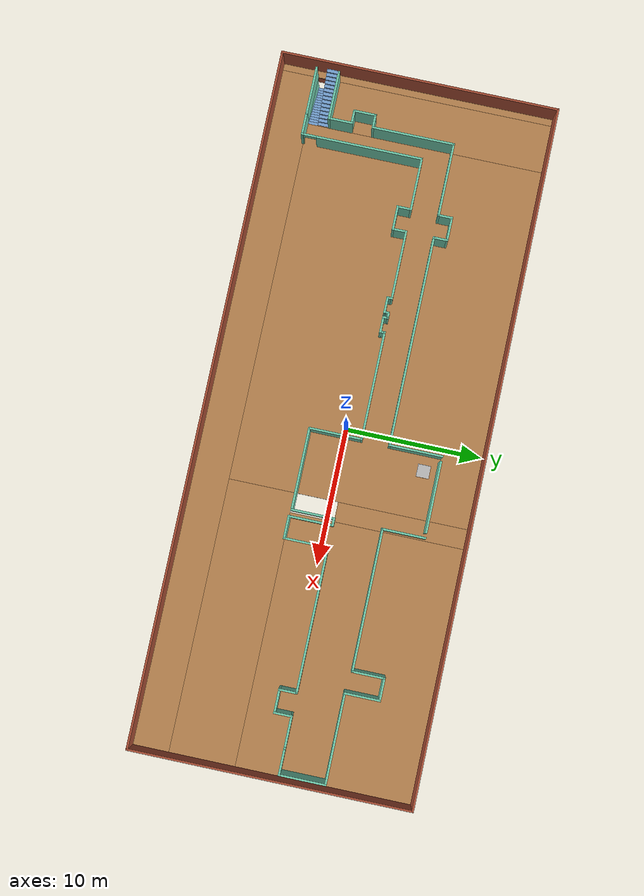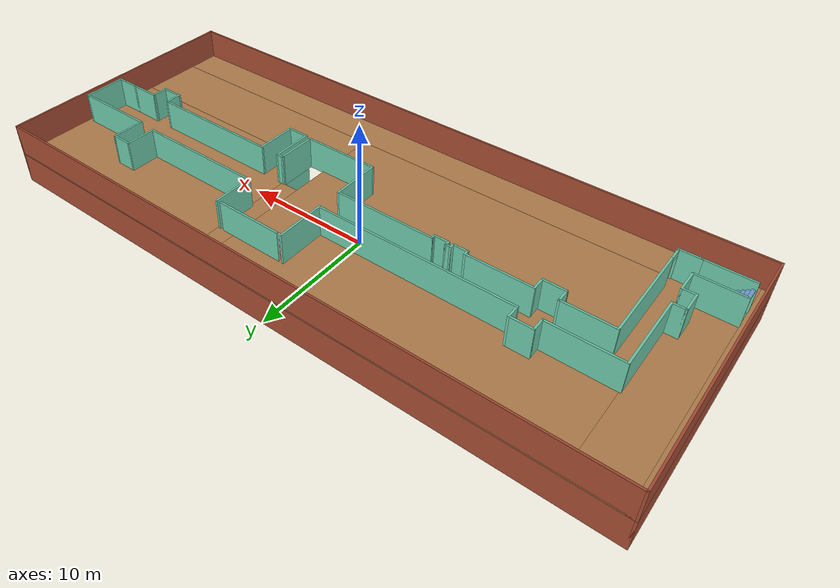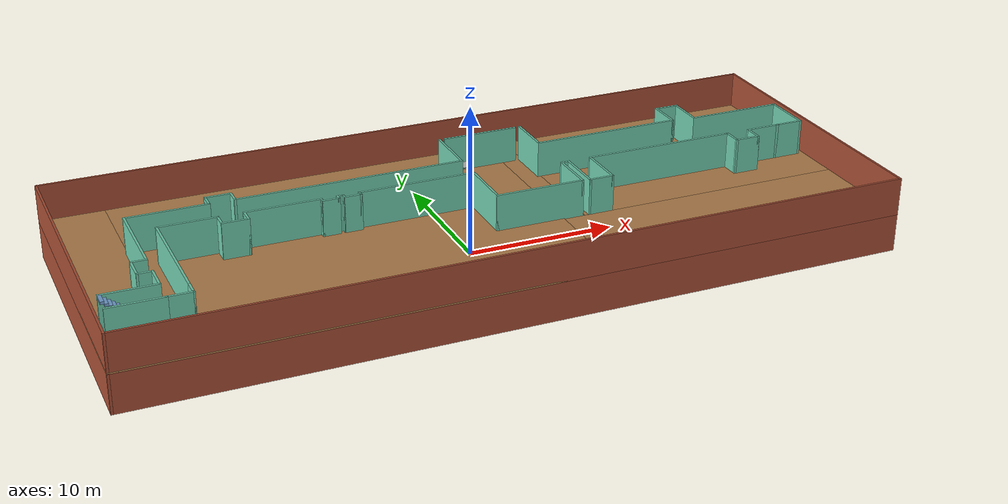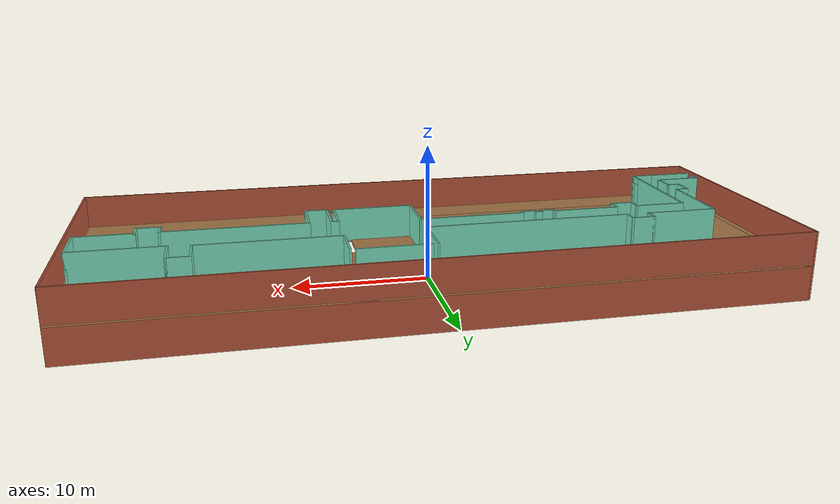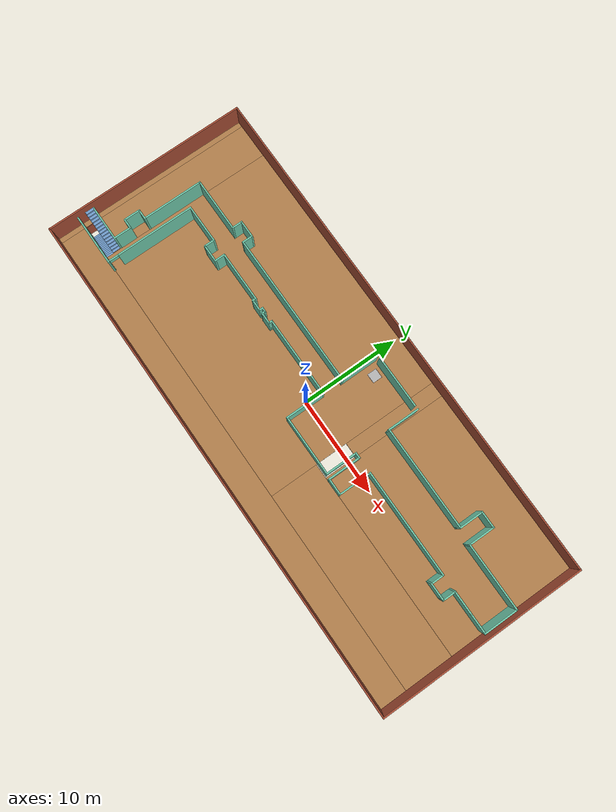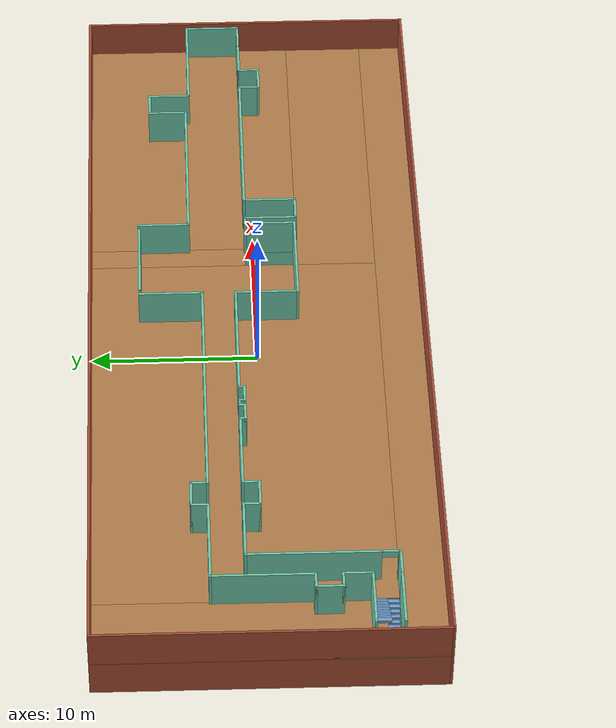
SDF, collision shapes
<?xml version='1.0'?>
<sdf version='1.7'>
  <model name='Version_precise_map_gazebo'>
    <pose>0 0 0 0 -0 0</pose>
    <link name='Floor_1'>
      <pose>0 0 2.5 0 -0 0</pose>
      <visual name='Floor_1_Visual_0'>
        <pose>-24.7594 0 0.05 0 -0 0</pose>
        <geometry>
          <box>
            <size>0.631175 20.15 0.1</size>
          </box>
        </geometry>
        <material>
          <script>
            <uri>file://media/materials/scripts/gazebo.material</uri>
            <name>Gazebo/Wood</name>
          </script>
          <ambient>1 1 1 1</ambient>
        </material>
        <meta>
          <layer>1</layer>
        </meta>
      </visual>
      <collision name='Floor_1_Collision_0'>
        <geometry>
          <box>
            <size>0.631175 20.15 0.1</size>
          </box>
        </geometry>
        <pose>-24.7594 0 0.05 0 -0 0</pose>
      </collision>
      <visual name='Floor_1_Visual_1'>
        <pose>0.315588 -8.71984 0.05 0 -0 0</pose>
        <geometry>
          <box>
            <size>49.5188 2.71032 0.1</size>
          </box>
        </geometry>
        <material>
          <script>
            <uri>file://media/materials/scripts/gazebo.material</uri>
            <name>Gazebo/Wood</name>
          </script>
          <ambient>1 1 1 1</ambient>
        </material>
        <meta>
          <layer>1</layer>
        </meta>
      </visual>
      <collision name='Floor_1_Collision_1'>
        <geometry>
          <box>
            <size>49.5188 2.71032 0.1</size>
          </box>
        </geometry>
        <pose>0.315588 -8.71984 0.05 0 -0 0</pose>
      </collision>
      <visual name='Floor_1_Visual_2'>
        <pose>-6.8976 1.35516 0.05 0 -0 0</pose>
        <geometry>
          <box>
            <size>28.0924 17.4397 0.1</size> <!-- Augmenter vers la droite de 1.8 -->
          </box>
        </geometry>
        <material>
          <script>
            <uri>file://media/materials/scripts/gazebo.material</uri>
            <name>Gazebo/Wood</name>
          </script>
          <ambient>1 1 1 1</ambient>
        </material>
        <meta>
          <layer>1</layer>
        </meta>
      </visual>
      <collision name='Floor_1_Collision_2'>
        <geometry>
          <box>
            <size>26.2924 17.4397 0.1</size>
          </box>
        </geometry>
        <pose>-7.7976 1.35516 0.05 0 -0 0</pose>
      </collision>
      <visual name='Floor_1_Visual_3'>
        <pose>16.1118 -4.98908 0.05 0 -0 0</pose>
        <geometry>
          <box>
            <size>17.9264 4.7512 0.1</size> <!-- Rétrécir vers la droite de 1.8 -->
          </box>
        </geometry>
        <material>
          <script>
            <uri>file://media/materials/scripts/gazebo.material</uri>
            <name>Gazebo/Wood</name>
          </script>
          <ambient>1 1 1 1</ambient>
        </material>
        <meta>
          <layer>1</layer>
        </meta>
      </visual>
      <collision name='Floor_1_Collision_3'>
        <geometry>
          <box>
            <size>19.7264 4.7512 0.1</size>
          </box>
        </geometry>
        <pose>15.2118 -4.98908 0.05 0 -0 0</pose>
      </collision>
      <visual name='Floor_1_Visual_4'>
        <pose>-22.6938 1.76016 0.05 0 -0 0</pose>
        <geometry>
          <box>
            <size>3.5 16.6297 0.1</size>
          </box>
        </geometry>
        <material>
          <script>
            <uri>file://media/materials/scripts/gazebo.material</uri>
            <name>Gazebo/Wood</name>
          </script>
          <ambient>1 1 1 1</ambient>
        </material>
        <meta>
          <layer>1</layer>
        </meta>
      </visual>
      <collision name='Floor_1_Collision_4'>
        <geometry>
          <box>
            <size>3.5 16.6297 0.1</size>
          </box>
        </geometry>
        <pose>-22.6938 1.76016 0.05 0 -0 0</pose>
      </collision>
      <visual name='Floor_1_Visual_5'>
        <pose>16.8238 3.73076 0.05 0 -0 0</pose>
        <geometry>
          <box>
            <size>16.5025 12.6885 0.1</size> <!-- Rétrécir vers la droite de 1.8 -->
          </box>
        </geometry>
        <material>
          <script>
            <uri>file://media/materials/scripts/gazebo.material</uri>
            <name>Gazebo/Wood</name>
          </script>
          <ambient>1 1 1 1</ambient>
        </material>
        <meta>
          <layer>1</layer>
        </meta>
      </visual>
      <collision name='Floor_1_Collision_5'>
        <geometry>
          <box>
            <size>18.3025 12.6885 0.1</size>
          </box>
        </geometry>
        <pose>15.9238 3.73076 0.05 0 -0 0</pose>
      </collision>
      <visual name='Floor_1_Visual_6'>
        <pose>7.86056 5.3225 0.05 0 -0 0</pose>
        <geometry>
          <box>
            <size>1.42389 9.505 0.1</size> <!-- Décaler vers la droite de 1.8 -->
          </box>
        </geometry>
        <material>
          <script>
            <uri>file://media/materials/scripts/gazebo.material</uri>
            <name>Gazebo/Wood</name>
          </script>
          <ambient>1 1 1 1</ambient>
        </material>
        <meta>
          <layer>1</layer>
        </meta>
      </visual>
      <collision name='Floor_1_Collision_6'>
        <geometry>
          <box>
            <size>1.42389 9.505 0.1</size>
          </box>
        </geometry>
        <pose>6.06056 5.3225 0.05 0 -0 0</pose>
      </collision>
    </link>
    <link name='Stairs_0'>
      <visual name='Stairs_0_Visual_0'>
        <pose>7.86056 -2.50736 0.083333 0 -0 -3.14159</pose>
        <geometry>
          <box>
            <size>1.42389 0.212232 0.166667</size>
          </box>
        </geometry>
        <material>
          <script>
            <uri>file://media/materials/scripts/gazebo.material</uri>
            <name>Gazebo/Grey</name>
          </script>
          <ambient>0.12549 0.290196 0.529412 1</ambient>
        </material>
        <meta>
          <layer>0</layer>
        </meta>
      </visual>
      <collision name='Stairs_0_Collision_0'>
        <geometry>
          <box>
            <size>1.42389 0.212232 0.166667</size>
          </box>
        </geometry>
        <pose>7.86056 -2.50736 0.083333 0 -0 -3.14159</pose>
      </collision>
      <visual name='Stairs_0_Visual_1'>
        <pose>7.86056 -2.29513 0.25 0 -0 -3.14159</pose>
        <geometry>
          <box>
            <size>1.42389 0.212232 0.166667</size>
          </box>
        </geometry>
        <material>
          <script>
            <uri>file://media/materials/scripts/gazebo.material</uri>
            <name>Gazebo/Grey</name>
          </script>
          <ambient>0.12549 0.290196 0.529412 1</ambient>
        </material>
        <meta>
          <layer>0</layer>
        </meta>
      </visual>
      <collision name='Stairs_0_Collision_1'>
        <geometry>
          <box>
            <size>1.42389 0.212232 0.166667</size>
          </box>
        </geometry>
        <pose>7.86056 -2.29513 0.25 0 -0 -3.14159</pose>
      </collision>
      <visual name='Stairs_0_Visual_2'>
        <pose>7.86056 -2.0829 0.416667 0 -0 -3.14159</pose>
        <geometry>
          <box>
            <size>1.42389 0.212232 0.166667</size>
          </box>
        </geometry>
        <material>
          <script>
            <uri>file://media/materials/scripts/gazebo.material</uri>
            <name>Gazebo/Grey</name>
          </script>
          <ambient>0.12549 0.290196 0.529412 1</ambient>
        </material>
        <meta>
          <layer>0</layer>
        </meta>
      </visual>
      <collision name='Stairs_0_Collision_2'>
        <geometry>
          <box>
            <size>1.42389 0.212232 0.166667</size>
          </box>
        </geometry>
        <pose>7.86056 -2.0829 0.416667 0 -0 -3.14159</pose>
      </collision>
      <visual name='Stairs_0_Visual_3'>
        <pose>7.86056 -1.87067 0.583333 0 -0 -3.14159</pose>
        <geometry>
          <box>
            <size>1.42389 0.212232 0.166667</size>
          </box>
        </geometry>
        <material>
          <script>
            <uri>file://media/materials/scripts/gazebo.material</uri>
            <name>Gazebo/Grey</name>
          </script>
          <ambient>0.12549 0.290196 0.529412 1</ambient>
        </material>
        <meta>
          <layer>0</layer>
        </meta>
      </visual>
      <collision name='Stairs_0_Collision_3'>
        <geometry>
          <box>
            <size>1.42389 0.212232 0.166667</size>
          </box>
        </geometry>
        <pose>7.86056 -1.87067 0.583333 0 -0 -3.14159</pose>
      </collision>
      <visual name='Stairs_0_Visual_4'>
        <pose>7.86056 -1.65844 0.75 0 -0 -3.14159</pose>
        <geometry>
          <box>
            <size>1.42389 0.212232 0.166667</size>
          </box>
        </geometry>
        <material>
          <script>
            <uri>file://media/materials/scripts/gazebo.material</uri>
            <name>Gazebo/Grey</name>
          </script>
          <ambient>0.12549 0.290196 0.529412 1</ambient>
        </material>
        <meta>
          <layer>0</layer>
        </meta>
      </visual>
      <collision name='Stairs_0_Collision_4'>
        <geometry>
          <box>
            <size>1.42389 0.212232 0.166667</size>
          </box>
        </geometry>
        <pose>7.86056 -1.65844 0.75 0 -0 -3.14159</pose>
      </collision>
      <visual name='Stairs_0_Visual_5'>
        <pose>7.86056 -1.4462 0.916667 0 -0 -3.14159</pose>
        <geometry>
          <box>
            <size>1.42389 0.212232 0.166667</size>
          </box>
        </geometry>
        <material>
          <script>
            <uri>file://media/materials/scripts/gazebo.material</uri>
            <name>Gazebo/Grey</name>
          </script>
          <ambient>0.12549 0.290196 0.529412 1</ambient>
        </material>
        <meta>
          <layer>0</layer>
        </meta>
      </visual>
      <collision name='Stairs_0_Collision_5'>
        <geometry>
          <box>
            <size>1.42389 0.212232 0.166667</size>
          </box>
        </geometry>
        <pose>7.86056 -1.4462 0.916667 0 -0 -3.14159</pose>
      </collision>
      <visual name='Stairs_0_Visual_6'>
        <pose>7.86056 -1.23397 1.08333 0 -0 -3.14159</pose>
        <geometry>
          <box>
            <size>1.42389 0.212232 0.166667</size>
          </box>
        </geometry>
        <material>
          <script>
            <uri>file://media/materials/scripts/gazebo.material</uri>
            <name>Gazebo/Grey</name>
          </script>
          <ambient>0.12549 0.290196 0.529412 1</ambient>
        </material>
        <meta>
          <layer>0</layer>
        </meta>
      </visual>
      <collision name='Stairs_0_Collision_6'>
        <geometry>
          <box>
            <size>1.42389 0.212232 0.166667</size>
          </box>
        </geometry>
        <pose>7.86056 -1.23397 1.08333 0 -0 -3.14159</pose>
      </collision>
      <visual name='Stairs_0_Visual_7'>
        <pose>7.86056 -1.02174 1.25 0 -0 -3.14159</pose>
        <geometry>
          <box>
            <size>1.42389 0.212232 0.166667</size>
          </box>
        </geometry>
        <material>
          <script>
            <uri>file://media/materials/scripts/gazebo.material</uri>
            <name>Gazebo/Grey</name>
          </script>
          <ambient>0.12549 0.290196 0.529412 1</ambient>
        </material>
        <meta>
          <layer>0</layer>
        </meta>
      </visual>
      <collision name='Stairs_0_Collision_7'>
        <geometry>
          <box>
            <size>1.42389 0.212232 0.166667</size>
          </box>
        </geometry>
        <pose>7.86056 -1.02174 1.25 0 -0 -3.14159</pose>
      </collision>
      <visual name='Stairs_0_Visual_8'>
        <pose>7.86056 -0.809507 1.41667 0 -0 -3.14159</pose>
        <geometry>
          <box>
            <size>1.42389 0.212232 0.166667</size>
          </box>
        </geometry>
        <material>
          <script>
            <uri>file://media/materials/scripts/gazebo.material</uri>
            <name>Gazebo/Grey</name>
          </script>
          <ambient>0.12549 0.290196 0.529412 1</ambient>
        </material>
        <meta>
          <layer>0</layer>
        </meta>
      </visual>
      <collision name='Stairs_0_Collision_8'>
        <geometry>
          <box>
            <size>1.42389 0.212232 0.166667</size>
          </box>
        </geometry>
        <pose>7.86056 -0.809507 1.41667 0 -0 -3.14159</pose>
      </collision>
      <visual name='Stairs_0_Visual_9'>
        <pose>7.86056 -0.597275 1.58333 0 -0 -3.14159</pose>
        <geometry>
          <box>
            <size>1.42389 0.212232 0.166667</size>
          </box>
        </geometry>
        <material>
          <script>
            <uri>file://media/materials/scripts/gazebo.material</uri>
            <name>Gazebo/Grey</name>
          </script>
          <ambient>0.12549 0.290196 0.529412 1</ambient>
        </material>
        <meta>
          <layer>0</layer>
        </meta>
      </visual>
      <collision name='Stairs_0_Collision_9'>
        <geometry>
          <box>
            <size>1.42389 0.212232 0.166667</size>
          </box>
        </geometry>
        <pose>7.86056 -0.597275 1.58333 0 -0 -3.14159</pose>
      </collision>
      <visual name='Stairs_0_Visual_10'>
        <pose>7.86056 -0.385043 1.75 0 -0 -3.14159</pose>
        <geometry>
          <box>
            <size>1.42389 0.212232 0.166667</size>
          </box>
        </geometry>
        <material>
          <script>
            <uri>file://media/materials/scripts/gazebo.material</uri>
            <name>Gazebo/Grey</name>
          </script>
          <ambient>0.12549 0.290196 0.529412 1</ambient>
        </material>
        <meta>
          <layer>0</layer>
        </meta>
      </visual>
      <collision name='Stairs_0_Collision_10'>
        <geometry>
          <box>
            <size>1.42389 0.212232 0.166667</size>
          </box>
        </geometry>
        <pose>7.86056 -0.385043 1.75 0 -0 -3.14159</pose>
      </collision>
      <visual name='Stairs_0_Visual_11'>
        <pose>7.86056 -0.172812 1.91667 0 -0 -3.14159</pose>
        <geometry>
          <box>
            <size>1.42389 0.212232 0.166667</size>
          </box>
        </geometry>
        <material>
          <script>
            <uri>file://media/materials/scripts/gazebo.material</uri>
            <name>Gazebo/Grey</name>
          </script>
          <ambient>0.12549 0.290196 0.529412 1</ambient>
        </material>
        <meta>
          <layer>0</layer>
        </meta>
      </visual>
      <collision name='Stairs_0_Collision_11'>
        <geometry>
          <box>
            <size>1.42389 0.212232 0.166667</size>
          </box>
        </geometry>
        <pose>7.86056 -0.172812 1.91667 0 -0 -3.14159</pose>
      </collision>
      <visual name='Stairs_0_Visual_12'>
        <pose>7.86056 0.03942 2.08333 0 -0 -3.14159</pose>
        <geometry>
          <box>
            <size>1.42389 0.212232 0.166667</size>
          </box>
        </geometry>
        <material>
          <script>
            <uri>file://media/materials/scripts/gazebo.material</uri>
            <name>Gazebo/Grey</name>
          </script>
          <ambient>0.12549 0.290196 0.529412 1</ambient>
        </material>
        <meta>
          <layer>0</layer>
        </meta>
      </visual>
      <collision name='Stairs_0_Collision_12'>
        <geometry>
          <box>
            <size>1.42389 0.212232 0.166667</size>
          </box>
        </geometry>
        <pose>7.86056 0.03942 2.08333 0 -0 -3.14159</pose>
      </collision>
      <visual name='Stairs_0_Visual_13'>
        <pose>7.86056 0.251652 2.25 0 -0 -3.14159</pose>
        <geometry>
          <box>
            <size>1.42389 0.212232 0.166667</size>
          </box>
        </geometry>
        <material>
          <script>
            <uri>file://media/materials/scripts/gazebo.material</uri>
            <name>Gazebo/Grey</name>
          </script>
          <ambient>0.12549 0.290196 0.529412 1</ambient>
        </material>
        <meta>
          <layer>0</layer>
        </meta>
      </visual>
      <collision name='Stairs_0_Collision_13'>
        <geometry>
          <box>
            <size>1.42389 0.212232 0.166667</size>
          </box>
        </geometry>
        <pose>7.86056 0.251652 2.25 0 -0 -3.14159</pose>
      </collision>
      <visual name='Stairs_0_Visual_14'>
        <pose>7.86056 0.463884 2.41667 0 -0 -3.14159</pose>
        <geometry>
          <box>
            <size>1.42389 0.212232 0.166667</size>
          </box>
        </geometry>
        <material>
          <script>
            <uri>file://media/materials/scripts/gazebo.material</uri>
            <name>Gazebo/Grey</name>
          </script>
          <ambient>0.12549 0.290196 0.529412 1</ambient>
        </material>
        <meta>
          <layer>0</layer>
        </meta>
      </visual>
      <collision name='Stairs_0_Collision_14'>
        <geometry>
          <box>
            <size>1.42389 0.212232 0.166667</size>
          </box>
        </geometry>
        <pose>7.86056 0.463884 2.41667 0 -0 -3.14159</pose>
      </collision>
    </link>
    <link name='Stairs_1'>
      <visual name='Stairs_1_Visual_0'>
        <pose>-24.3272 -6.95968 0.083333 0 -0 1.5708</pose>
        <geometry>
          <box>
            <size>0.81 0.233333 0.166667</size>
          </box>
        </geometry>
        <material>
          <script>
            <uri>file://media/materials/scripts/gazebo.material</uri>
            <name>Gazebo/Grey</name>
          </script>
          <ambient>0.447059 0.623529 0.811765 1</ambient>
        </material>
        <meta>
          <layer>0</layer>
        </meta>
      </visual>
      <collision name='Stairs_1_Collision_0'>
        <geometry>
          <box>
            <size>0.81 0.233333 0.166667</size>
          </box>
        </geometry>
        <pose>-24.3272 -6.95968 0.083333 0 -0 1.5708</pose>
      </collision>
      <visual name='Stairs_1_Visual_1'>
        <pose>-24.0938 -6.95968 0.25 0 -0 1.5708</pose>
        <geometry>
          <box>
            <size>0.81 0.233333 0.166667</size>
          </box>
        </geometry>
        <material>
          <script>
            <uri>file://media/materials/scripts/gazebo.material</uri>
            <name>Gazebo/Grey</name>
          </script>
          <ambient>0.447059 0.623529 0.811765 1</ambient>
        </material>
        <meta>
          <layer>0</layer>
        </meta>
      </visual>
      <collision name='Stairs_1_Collision_1'>
        <geometry>
          <box>
            <size>0.81 0.233333 0.166667</size>
          </box>
        </geometry>
        <pose>-24.0938 -6.95968 0.25 0 -0 1.5708</pose>
      </collision>
      <visual name='Stairs_1_Visual_2'>
        <pose>-23.8605 -6.95968 0.416667 0 -0 1.5708</pose>
        <geometry>
          <box>
            <size>0.81 0.233333 0.166667</size>
          </box>
        </geometry>
        <material>
          <script>
            <uri>file://media/materials/scripts/gazebo.material</uri>
            <name>Gazebo/Grey</name>
          </script>
          <ambient>0.447059 0.623529 0.811765 1</ambient>
        </material>
        <meta>
          <layer>0</layer>
        </meta>
      </visual>
      <collision name='Stairs_1_Collision_2'>
        <geometry>
          <box>
            <size>0.81 0.233333 0.166667</size>
          </box>
        </geometry>
        <pose>-23.8605 -6.95968 0.416667 0 -0 1.5708</pose>
      </collision>
      <visual name='Stairs_1_Visual_3'>
        <pose>-23.6272 -6.95968 0.583333 0 -0 1.5708</pose>
        <geometry>
          <box>
            <size>0.81 0.233333 0.166667</size>
          </box>
        </geometry>
        <material>
          <script>
            <uri>file://media/materials/scripts/gazebo.material</uri>
            <name>Gazebo/Grey</name>
          </script>
          <ambient>0.447059 0.623529 0.811765 1</ambient>
        </material>
        <meta>
          <layer>0</layer>
        </meta>
      </visual>
      <collision name='Stairs_1_Collision_3'>
        <geometry>
          <box>
            <size>0.81 0.233333 0.166667</size>
          </box>
        </geometry>
        <pose>-23.6272 -6.95968 0.583333 0 -0 1.5708</pose>
      </collision>
      <visual name='Stairs_1_Visual_4'>
        <pose>-23.3938 -6.95968 0.75 0 -0 1.5708</pose>
        <geometry>
          <box>
            <size>0.81 0.233333 0.166667</size>
          </box>
        </geometry>
        <material>
          <script>
            <uri>file://media/materials/scripts/gazebo.material</uri>
            <name>Gazebo/Grey</name>
          </script>
          <ambient>0.447059 0.623529 0.811765 1</ambient>
        </material>
        <meta>
          <layer>0</layer>
        </meta>
      </visual>
      <collision name='Stairs_1_Collision_4'>
        <geometry>
          <box>
            <size>0.81 0.233333 0.166667</size>
          </box>
        </geometry>
        <pose>-23.3938 -6.95968 0.75 0 -0 1.5708</pose>
      </collision>
      <visual name='Stairs_1_Visual_5'>
        <pose>-23.1605 -6.95968 0.916667 0 -0 1.5708</pose>
        <geometry>
          <box>
            <size>0.81 0.233333 0.166667</size>
          </box>
        </geometry>
        <material>
          <script>
            <uri>file://media/materials/scripts/gazebo.material</uri>
            <name>Gazebo/Grey</name>
          </script>
          <ambient>0.447059 0.623529 0.811765 1</ambient>
        </material>
        <meta>
          <layer>0</layer>
        </meta>
      </visual>
      <collision name='Stairs_1_Collision_5'>
        <geometry>
          <box>
            <size>0.81 0.233333 0.166667</size>
          </box>
        </geometry>
        <pose>-23.1605 -6.95968 0.916667 0 -0 1.5708</pose>
      </collision>
      <visual name='Stairs_1_Visual_6'>
        <pose>-22.9272 -6.95968 1.08333 0 -0 1.5708</pose>
        <geometry>
          <box>
            <size>0.81 0.233333 0.166667</size>
          </box>
        </geometry>
        <material>
          <script>
            <uri>file://media/materials/scripts/gazebo.material</uri>
            <name>Gazebo/Grey</name>
          </script>
          <ambient>0.447059 0.623529 0.811765 1</ambient>
        </material>
        <meta>
          <layer>0</layer>
        </meta>
      </visual>
      <collision name='Stairs_1_Collision_6'>
        <geometry>
          <box>
            <size>0.81 0.233333 0.166667</size>
          </box>
        </geometry>
        <pose>-22.9272 -6.95968 1.08333 0 -0 1.5708</pose>
      </collision>
      <visual name='Stairs_1_Visual_7'>
        <pose>-22.6938 -6.95968 1.25 0 -0 1.5708</pose>
        <geometry>
          <box>
            <size>0.81 0.233333 0.166667</size>
          </box>
        </geometry>
        <material>
          <script>
            <uri>file://media/materials/scripts/gazebo.material</uri>
            <name>Gazebo/Grey</name>
          </script>
          <ambient>0.447059 0.623529 0.811765 1</ambient>
        </material>
        <meta>
          <layer>0</layer>
        </meta>
      </visual>
      <collision name='Stairs_1_Collision_7'>
        <geometry>
          <box>
            <size>0.81 0.233333 0.166667</size>
          </box>
        </geometry>
        <pose>-22.6938 -6.95968 1.25 0 -0 1.5708</pose>
      </collision>
      <visual name='Stairs_1_Visual_8'>
        <pose>-22.4605 -6.95968 1.41667 0 -0 1.5708</pose>
        <geometry>
          <box>
            <size>0.81 0.233333 0.166667</size>
          </box>
        </geometry>
        <material>
          <script>
            <uri>file://media/materials/scripts/gazebo.material</uri>
            <name>Gazebo/Grey</name>
          </script>
          <ambient>0.447059 0.623529 0.811765 1</ambient>
        </material>
        <meta>
          <layer>0</layer>
        </meta>
      </visual>
      <collision name='Stairs_1_Collision_8'>
        <geometry>
          <box>
            <size>0.81 0.233333 0.166667</size>
          </box>
        </geometry>
        <pose>-22.4605 -6.95968 1.41667 0 -0 1.5708</pose>
      </collision>
      <visual name='Stairs_1_Visual_9'>
        <pose>-22.2272 -6.95968 1.58333 0 -0 1.5708</pose>
        <geometry>
          <box>
            <size>0.81 0.233333 0.166667</size>
          </box>
        </geometry>
        <material>
          <script>
            <uri>file://media/materials/scripts/gazebo.material</uri>
            <name>Gazebo/Grey</name>
          </script>
          <ambient>0.447059 0.623529 0.811765 1</ambient>
        </material>
        <meta>
          <layer>0</layer>
        </meta>
      </visual>
      <collision name='Stairs_1_Collision_9'>
        <geometry>
          <box>
            <size>0.81 0.233333 0.166667</size>
          </box>
        </geometry>
        <pose>-22.2272 -6.95968 1.58333 0 -0 1.5708</pose>
      </collision>
      <visual name='Stairs_1_Visual_10'>
        <pose>-21.9938 -6.95968 1.75 0 -0 1.5708</pose>
        <geometry>
          <box>
            <size>0.81 0.233333 0.166667</size>
          </box>
        </geometry>
        <material>
          <script>
            <uri>file://media/materials/scripts/gazebo.material</uri>
            <name>Gazebo/Grey</name>
          </script>
          <ambient>0.447059 0.623529 0.811765 1</ambient>
        </material>
        <meta>
          <layer>0</layer>
        </meta>
      </visual>
      <collision name='Stairs_1_Collision_10'>
        <geometry>
          <box>
            <size>0.81 0.233333 0.166667</size>
          </box>
        </geometry>
        <pose>-21.9938 -6.95968 1.75 0 -0 1.5708</pose>
      </collision>
      <visual name='Stairs_1_Visual_11'>
        <pose>-21.7605 -6.95968 1.91667 0 -0 1.5708</pose>
        <geometry>
          <box>
            <size>0.81 0.233333 0.166667</size>
          </box>
        </geometry>
        <material>
          <script>
            <uri>file://media/materials/scripts/gazebo.material</uri>
            <name>Gazebo/Grey</name>
          </script>
          <ambient>0.447059 0.623529 0.811765 1</ambient>
        </material>
        <meta>
          <layer>0</layer>
        </meta>
      </visual>
      <collision name='Stairs_1_Collision_11'>
        <geometry>
          <box>
            <size>0.81 0.233333 0.166667</size>
          </box>
        </geometry>
        <pose>-21.7605 -6.95968 1.91667 0 -0 1.5708</pose>
      </collision>
      <visual name='Stairs_1_Visual_12'>
        <pose>-21.5272 -6.95968 2.08333 0 -0 1.5708</pose>
        <geometry>
          <box>
            <size>0.81 0.233333 0.166667</size>
          </box>
        </geometry>
        <material>
          <script>
            <uri>file://media/materials/scripts/gazebo.material</uri>
            <name>Gazebo/Grey</name>
          </script>
          <ambient>0.447059 0.623529 0.811765 1</ambient>
        </material>
        <meta>
          <layer>0</layer>
        </meta>
      </visual>
      <collision name='Stairs_1_Collision_12'>
        <geometry>
          <box>
            <size>0.81 0.233333 0.166667</size>
          </box>
        </geometry>
        <pose>-21.5272 -6.95968 2.08333 0 -0 1.5708</pose>
      </collision>
      <visual name='Stairs_1_Visual_13'>
        <pose>-21.2938 -6.95968 2.25 0 -0 1.5708</pose>
        <geometry>
          <box>
            <size>0.81 0.233333 0.166667</size>
          </box>
        </geometry>
        <material>
          <script>
            <uri>file://media/materials/scripts/gazebo.material</uri>
            <name>Gazebo/Grey</name>
          </script>
          <ambient>0.447059 0.623529 0.811765 1</ambient>
        </material>
        <meta>
          <layer>0</layer>
        </meta>
      </visual>
      <collision name='Stairs_1_Collision_13'>
        <geometry>
          <box>
            <size>0.81 0.233333 0.166667</size>
          </box>
        </geometry>
        <pose>-21.2938 -6.95968 2.25 0 -0 1.5708</pose>
      </collision>
      <visual name='Stairs_1_Visual_14'>
        <pose>-21.0605 -6.95968 2.41667 0 -0 1.5708</pose>
        <geometry>
          <box>
            <size>0.81 0.233333 0.166667</size>
          </box>
        </geometry>
        <material>
          <script>
            <uri>file://media/materials/scripts/gazebo.material</uri>
            <name>Gazebo/Grey</name>
          </script>
          <ambient>0.447059 0.623529 0.811765 1</ambient>
        </material>
        <meta>
          <layer>0</layer>
        </meta>
      </visual>
      <collision name='Stairs_1_Collision_14'>
        <geometry>
          <box>
            <size>0.81 0.233333 0.166667</size>
          </box>
        </geometry>
        <pose>-21.0605 -6.95968 2.41667 0 -0 1.5708</pose>
      </collision>
    </link>
    <link name='Stairs_2'>
      <visual name='Stairs_2_Visual_0'>
        <pose>-21.0867 -6.202 2.58333 0 -0 -1.5708</pose>
        <geometry>
          <box>
            <size>0.81 0.233333 0.166667</size>
          </box>
        </geometry>
        <material>
          <script>
            <uri>file://media/materials/scripts/gazebo.material</uri>
            <name>Gazebo/Grey</name>
          </script>
          <ambient>0.447059 0.623529 0.811765 1</ambient>
        </material>
        <meta>
          <layer>1</layer>
        </meta>
      </visual>
      <collision name='Stairs_2_Collision_0'>
        <geometry>
          <box>
            <size>0.81 0.233333 0.166667</size>
          </box>
        </geometry>
        <pose>-21.0867 -6.202 2.58333 0 -0 -1.5708</pose>
      </collision>
      <visual name='Stairs_2_Visual_1'>
        <pose>-21.32 -6.202 2.75 0 -0 -1.5708</pose>
        <geometry>
          <box>
            <size>0.81 0.233333 0.166667</size>
          </box>
        </geometry>
        <material>
          <script>
            <uri>file://media/materials/scripts/gazebo.material</uri>
            <name>Gazebo/Grey</name>
          </script>
          <ambient>0.447059 0.623529 0.811765 1</ambient>
        </material>
        <meta>
          <layer>1</layer>
        </meta>
      </visual>
      <collision name='Stairs_2_Collision_1'>
        <geometry>
          <box>
            <size>0.81 0.233333 0.166667</size>
          </box>
        </geometry>
        <pose>-21.32 -6.202 2.75 0 -0 -1.5708</pose>
      </collision>
      <visual name='Stairs_2_Visual_2'>
        <pose>-21.5533 -6.202 2.91667 0 -0 -1.5708</pose>
        <geometry>
          <box>
            <size>0.81 0.233333 0.166667</size>
          </box>
        </geometry>
        <material>
          <script>
            <uri>file://media/materials/scripts/gazebo.material</uri>
            <name>Gazebo/Grey</name>
          </script>
          <ambient>0.447059 0.623529 0.811765 1</ambient>
        </material>
        <meta>
          <layer>1</layer>
        </meta>
      </visual>
      <collision name='Stairs_2_Collision_2'>
        <geometry>
          <box>
            <size>0.81 0.233333 0.166667</size>
          </box>
        </geometry>
        <pose>-21.5533 -6.202 2.91667 0 -0 -1.5708</pose>
      </collision>
      <visual name='Stairs_2_Visual_3'>
        <pose>-21.7867 -6.202 3.08333 0 -0 -1.5708</pose>
        <geometry>
          <box>
            <size>0.81 0.233333 0.166667</size>
          </box>
        </geometry>
        <material>
          <script>
            <uri>file://media/materials/scripts/gazebo.material</uri>
            <name>Gazebo/Grey</name>
          </script>
          <ambient>0.447059 0.623529 0.811765 1</ambient>
        </material>
        <meta>
          <layer>1</layer>
        </meta>
      </visual>
      <collision name='Stairs_2_Collision_3'>
        <geometry>
          <box>
            <size>0.81 0.233333 0.166667</size>
          </box>
        </geometry>
        <pose>-21.7867 -6.202 3.08333 0 -0 -1.5708</pose>
      </collision>
      <visual name='Stairs_2_Visual_4'>
        <pose>-22.02 -6.202 3.25 0 -0 -1.5708</pose>
        <geometry>
          <box>
            <size>0.81 0.233333 0.166667</size>
          </box>
        </geometry>
        <material>
          <script>
            <uri>file://media/materials/scripts/gazebo.material</uri>
            <name>Gazebo/Grey</name>
          </script>
          <ambient>0.447059 0.623529 0.811765 1</ambient>
        </material>
        <meta>
          <layer>1</layer>
        </meta>
      </visual>
      <collision name='Stairs_2_Collision_4'>
        <geometry>
          <box>
            <size>0.81 0.233333 0.166667</size>
          </box>
        </geometry>
        <pose>-22.02 -6.202 3.25 0 -0 -1.5708</pose>
      </collision>
      <visual name='Stairs_2_Visual_5'>
        <pose>-22.2533 -6.202 3.41667 0 -0 -1.5708</pose>
        <geometry>
          <box>
            <size>0.81 0.233333 0.166667</size>
          </box>
        </geometry>
        <material>
          <script>
            <uri>file://media/materials/scripts/gazebo.material</uri>
            <name>Gazebo/Grey</name>
          </script>
          <ambient>0.447059 0.623529 0.811765 1</ambient>
        </material>
        <meta>
          <layer>1</layer>
        </meta>
      </visual>
      <collision name='Stairs_2_Collision_5'>
        <geometry>
          <box>
            <size>0.81 0.233333 0.166667</size>
          </box>
        </geometry>
        <pose>-22.2533 -6.202 3.41667 0 -0 -1.5708</pose>
      </collision>
      <visual name='Stairs_2_Visual_6'>
        <pose>-22.4867 -6.202 3.58333 0 -0 -1.5708</pose>
        <geometry>
          <box>
            <size>0.81 0.233333 0.166667</size>
          </box>
        </geometry>
        <material>
          <script>
            <uri>file://media/materials/scripts/gazebo.material</uri>
            <name>Gazebo/Grey</name>
          </script>
          <ambient>0.447059 0.623529 0.811765 1</ambient>
        </material>
        <meta>
          <layer>1</layer>
        </meta>
      </visual>
      <collision name='Stairs_2_Collision_6'>
        <geometry>
          <box>
            <size>0.81 0.233333 0.166667</size>
          </box>
        </geometry>
        <pose>-22.4867 -6.202 3.58333 0 -0 -1.5708</pose>
      </collision>
      <visual name='Stairs_2_Visual_7'>
        <pose>-22.72 -6.202 3.75 0 -0 -1.5708</pose>
        <geometry>
          <box>
            <size>0.81 0.233333 0.166667</size>
          </box>
        </geometry>
        <material>
          <script>
            <uri>file://media/materials/scripts/gazebo.material</uri>
            <name>Gazebo/Grey</name>
          </script>
          <ambient>0.447059 0.623529 0.811765 1</ambient>
        </material>
        <meta>
          <layer>1</layer>
        </meta>
      </visual>
      <collision name='Stairs_2_Collision_7'>
        <geometry>
          <box>
            <size>0.81 0.233333 0.166667</size>
          </box>
        </geometry>
        <pose>-22.72 -6.202 3.75 0 -0 -1.5708</pose>
      </collision>
      <visual name='Stairs_2_Visual_8'>
        <pose>-22.9533 -6.202 3.91667 0 -0 -1.5708</pose>
        <geometry>
          <box>
            <size>0.81 0.233333 0.166667</size>
          </box>
        </geometry>
        <material>
          <script>
            <uri>file://media/materials/scripts/gazebo.material</uri>
            <name>Gazebo/Grey</name>
          </script>
          <ambient>0.447059 0.623529 0.811765 1</ambient>
        </material>
        <meta>
          <layer>1</layer>
        </meta>
      </visual>
      <collision name='Stairs_2_Collision_8'>
        <geometry>
          <box>
            <size>0.81 0.233333 0.166667</size>
          </box>
        </geometry>
        <pose>-22.9533 -6.202 3.91667 0 -0 -1.5708</pose>
      </collision>
      <visual name='Stairs_2_Visual_9'>
        <pose>-23.1867 -6.202 4.08333 0 -0 -1.5708</pose>
        <geometry>
          <box>
            <size>0.81 0.233333 0.166667</size>
          </box>
        </geometry>
        <material>
          <script>
            <uri>file://media/materials/scripts/gazebo.material</uri>
            <name>Gazebo/Grey</name>
          </script>
          <ambient>0.447059 0.623529 0.811765 1</ambient>
        </material>
        <meta>
          <layer>1</layer>
        </meta>
      </visual>
      <collision name='Stairs_2_Collision_9'>
        <geometry>
          <box>
            <size>0.81 0.233333 0.166667</size>
          </box>
        </geometry>
        <pose>-23.1867 -6.202 4.08333 0 -0 -1.5708</pose>
      </collision>
      <visual name='Stairs_2_Visual_10'>
        <pose>-23.42 -6.202 4.25 0 -0 -1.5708</pose>
        <geometry>
          <box>
            <size>0.81 0.233333 0.166667</size>
          </box>
        </geometry>
        <material>
          <script>
            <uri>file://media/materials/scripts/gazebo.material</uri>
            <name>Gazebo/Grey</name>
          </script>
          <ambient>0.447059 0.623529 0.811765 1</ambient>
        </material>
        <meta>
          <layer>1</layer>
        </meta>
      </visual>
      <collision name='Stairs_2_Collision_10'>
        <geometry>
          <box>
            <size>0.81 0.233333 0.166667</size>
          </box>
        </geometry>
        <pose>-23.42 -6.202 4.25 0 -0 -1.5708</pose>
      </collision>
      <visual name='Stairs_2_Visual_11'>
        <pose>-23.6533 -6.202 4.41667 0 -0 -1.5708</pose>
        <geometry>
          <box>
            <size>0.81 0.233333 0.166667</size>
          </box>
        </geometry>
        <material>
          <script>
            <uri>file://media/materials/scripts/gazebo.material</uri>
            <name>Gazebo/Grey</name>
          </script>
          <ambient>0.447059 0.623529 0.811765 1</ambient>
        </material>
        <meta>
          <layer>1</layer>
        </meta>
      </visual>
      <collision name='Stairs_2_Collision_11'>
        <geometry>
          <box>
            <size>0.81 0.233333 0.166667</size>
          </box>
        </geometry>
        <pose>-23.6533 -6.202 4.41667 0 -0 -1.5708</pose>
      </collision>
      <visual name='Stairs_2_Visual_12'>
        <pose>-23.8867 -6.202 4.58333 0 -0 -1.5708</pose>
        <geometry>
          <box>
            <size>0.81 0.233333 0.166667</size>
          </box>
        </geometry>
        <material>
          <script>
            <uri>file://media/materials/scripts/gazebo.material</uri>
            <name>Gazebo/Grey</name>
          </script>
          <ambient>0.447059 0.623529 0.811765 1</ambient>
        </material>
        <meta>
          <layer>1</layer>
        </meta>
      </visual>
      <collision name='Stairs_2_Collision_12'>
        <geometry>
          <box>
            <size>0.81 0.233333 0.166667</size>
          </box>
        </geometry>
        <pose>-23.8867 -6.202 4.58333 0 -0 -1.5708</pose>
      </collision>
      <visual name='Stairs_2_Visual_13'>
        <pose>-24.12 -6.202 4.75 0 -0 -1.5708</pose>
        <geometry>
          <box>
            <size>0.81 0.233333 0.166667</size>
          </box>
        </geometry>
        <material>
          <script>
            <uri>file://media/materials/scripts/gazebo.material</uri>
            <name>Gazebo/Grey</name>
          </script>
          <ambient>0.447059 0.623529 0.811765 1</ambient>
        </material>
        <meta>
          <layer>1</layer>
        </meta>
      </visual>
      <collision name='Stairs_2_Collision_13'>
        <geometry>
          <box>
            <size>0.81 0.233333 0.166667</size>
          </box>
        </geometry>
        <pose>-24.12 -6.202 4.75 0 -0 -1.5708</pose>
      </collision>
      <visual name='Stairs_2_Visual_14'>
        <pose>-24.3533 -6.202 4.91667 0 -0 -1.5708</pose>
        <geometry>
          <box>
            <size>0.81 0.233333 0.166667</size>
          </box>
        </geometry>
        <material>
          <script>
            <uri>file://media/materials/scripts/gazebo.material</uri>
            <name>Gazebo/Grey</name>
          </script>
          <ambient>0.447059 0.623529 0.811765 1</ambient>
        </material>
        <meta>
          <layer>1</layer>
        </meta>
      </visual>
      <collision name='Stairs_2_Collision_14'>
        <geometry>
          <box>
            <size>0.81 0.233333 0.166667</size>
          </box>
        </geometry>
        <pose>-24.3533 -6.202 4.91667 0 -0 -1.5708</pose>
      </collision>
    </link>
    <link name='Wall_0'>
      <collision name='Wall_0_Collision'>
        <geometry>
          <box>
            <size>50.15 0.15 2.5</size>
          </box>
        </geometry>
        <pose>0 0 1.25 0 -0 0</pose>
      </collision>
      <visual name='Wall_0_Visual'>
        <pose>0 0 1.25 0 -0 0</pose>
        <geometry>
          <box>
            <size>50.15 0.15 2.5</size>
          </box>
        </geometry>
        <material>
          <script>
            <uri>file://media/materials/scripts/gazebo.material</uri>
            <name>Gazebo/Bricks</name>
          </script>
          <ambient>1 1 1 1</ambient>
        </material>
        <meta>
          <layer>0</layer>
        </meta>
      </visual>
      <pose>0 10 0 0 -0 0</pose>
    </link>
    <link name='Wall_100'>
      <collision name='Wall_100_Collision'>
        <geometry>
          <box>
            <size>0.45 0.15 2.5</size>
          </box>
        </geometry>
        <pose>0 0 1.25 0 -0 0</pose>
      </collision>
      <visual name='Wall_100_Visual'>
        <pose>0 0 1.25 0 -0 0</pose>
        <geometry>
          <box>
            <size>0.45 0.15 2.5</size>
          </box>
        </geometry>
        <material>
          <script>
            <uri>file://media/materials/scripts/gazebo.material</uri>
            <name>Gazebo/Grey</name>
          </script>
          <ambient>0.435294 0.796078 0.67451 1</ambient>
        </material>
        <meta>
          <layer>1</layer>
        </meta>
        <transparency>0.5</transparency>
      </visual>
      <pose>-8.27 1.125 2.5 0 -0 1.5708</pose>
    </link>
    <link name='Wall_102'>
      <collision name='Wall_102_Collision'>
        <geometry>
          <box>
            <size>1.2 0.15 2.5</size>
          </box>
        </geometry>
        <pose>0 0 1.25 0 -0 0</pose>
      </collision>
      <visual name='Wall_102_Visual'>
        <pose>0 0 1.25 0 -0 0</pose>
        <geometry>
          <box>
            <size>1.2 0.15 2.5</size>
          </box>
        </geometry>
        <material>
          <script>
            <uri>file://media/materials/scripts/gazebo.material</uri>
            <name>Gazebo/Grey</name>
          </script>
          <ambient>0.435294 0.796078 0.67451 1</ambient>
        </material>
        <meta>
          <layer>1</layer>
        </meta>
        <transparency>0.5</transparency>
      </visual>
      <pose>-8.795 0.975 2.5 0 -0 3.14159</pose>
    </link>

    <link name='Wall_106'>
      <collision name='Wall_106_Collision'>
        <geometry>
          <box>
            <size>0.45 0.15 2.5</size>
          </box>
        </geometry>
        <pose>0 0 1.25 0 -0 0</pose>
      </collision>
      <visual name='Wall_106_Visual'>
        <pose>0 0 1.25 0 -0 0</pose>
        <geometry>
          <box>
            <size>0.45 0.15 2.5</size>
          </box>
        </geometry>
        <material>
          <script>
            <uri>file://media/materials/scripts/gazebo.material</uri>
            <name>Gazebo/Grey</name>
          </script>
          <ambient>0.435294 0.796078 0.67451 1</ambient>
        </material>
        <meta>
          <layer>1</layer>
        </meta>
        <transparency>0.5</transparency>
      </visual>
      <pose>-9.32 1.125 2.5 0 -0 1.5708</pose>
    </link>
    <link name='Wall_108'>
      <collision name='Wall_108_Collision'>
        <geometry>
          <box>
            <size>5 0.15 2.5</size>
          </box>
        </geometry>
        <pose>0 0 1.25 0 -0 0</pose>
      </collision>
      <visual name='Wall_108_Visual'>
        <pose>0 0 1.25 0 -0 0</pose>
        <geometry>
          <box>
            <size>5 0.15 2.5</size>
          </box>
        </geometry>
        <material>
          <script>
            <uri>file://media/materials/scripts/gazebo.material</uri>
            <name>Gazebo/Grey</name>
          </script>
          <ambient>0.435294 0.796078 0.67451 1</ambient>
        </material>
        <meta>
          <layer>1</layer>
        </meta>
        <transparency>0.5</transparency>
      </visual>
      <pose>-11.745 1.275 2.5 0 -0 3.14159</pose>
    </link>
    <link name='Wall_110'>
      <collision name='Wall_110_Collision'>
        <geometry>
          <box>
            <size>1.1 0.15 2.5</size>
          </box>
        </geometry>
        <pose>0 0 1.25 0 -0 0</pose>
      </collision>
      <visual name='Wall_110_Visual'>
        <pose>0 0 1.25 0 -0 0</pose>
        <geometry>
          <box>
            <size>1.1 0.15 2.5</size>
          </box>
        </geometry>
        <material>
          <script>
            <uri>file://media/materials/scripts/gazebo.material</uri>
            <name>Gazebo/Grey</name>
          </script>
          <ambient>0.435294 0.796078 0.67451 1</ambient>
        </material>
        <meta>
          <layer>1</layer>
        </meta>
        <transparency>0.5</transparency>
      </visual>
      <pose>-14.17 0.8 2.5 0 -0 -1.5708</pose>
    </link>
    <link name='Wall_112'>
      <collision name='Wall_112_Collision'>
        <geometry>
          <box>
            <size>1.78 0.15 2.5</size>
          </box>
        </geometry>
        <pose>0 0 1.25 0 -0 0</pose>
      </collision>
      <visual name='Wall_112_Visual'>
        <pose>0 0 1.25 0 -0 0</pose>
        <geometry>
          <box>
            <size>1.78 0.15 2.5</size>
          </box>
        </geometry>
        <material>
          <script>
            <uri>file://media/materials/scripts/gazebo.material</uri>
            <name>Gazebo/Grey</name>
          </script>
          <ambient>0.435294 0.796078 0.67451 1</ambient>
        </material>
        <meta>
          <layer>1</layer>
        </meta>
        <transparency>0.5</transparency>
      </visual>
      <pose>-14.985 0.325 2.5 0 -0 3.14159</pose>
    </link>
    <link name='Wall_114'>
      <collision name='Wall_114_Collision'>
        <geometry>
          <box>
            <size>1.1 0.15 2.5</size>
          </box>
        </geometry>
        <pose>0 0 1.25 0 -0 0</pose>
      </collision>
      <visual name='Wall_114_Visual'>
        <pose>0 0 1.25 0 -0 0</pose>
        <geometry>
          <box>
            <size>1.1 0.15 2.5</size>
          </box>
        </geometry>
        <material>
          <script>
            <uri>file://media/materials/scripts/gazebo.material</uri>
            <name>Gazebo/Grey</name>
          </script>
          <ambient>0.435294 0.796078 0.67451 1</ambient>
        </material>
        <meta>
          <layer>1</layer>
        </meta>
        <transparency>0.5</transparency>
      </visual>
      <pose>-15.8 0.8 2.5 0 -0 1.5708</pose>
    </link>
    <link name='Wall_116'>
      <collision name='Wall_116_Collision'>
        <geometry>
          <box>
            <size>3.85 0.15 2.5</size>
          </box>
        </geometry>
        <pose>0 0 1.25 0 -0 0</pose>
      </collision>
      <visual name='Wall_116_Visual'>
        <pose>0 0 1.25 0 -0 0</pose>
        <geometry>
          <box>
            <size>3.85 0.15 2.5</size>
          </box>
        </geometry>
        <material>
          <script>
            <uri>file://media/materials/scripts/gazebo.material</uri>
            <name>Gazebo/Grey</name>
          </script>
          <ambient>0.435294 0.796078 0.67451 1</ambient>
        </material>
        <meta>
          <layer>1</layer>
        </meta>
        <transparency>0.5</transparency>
      </visual>
      <pose>-17.65 1.275 2.5 0 -0 3.14159</pose>
    </link>
    <link name='Wall_118'>
      <collision name='Wall_118_Collision'>
        <geometry>
          <box>
            <size>3.875 0.15 2.5</size>
          </box>
        </geometry>
        <pose>0 0 1.25 0 -0 0</pose>
      </collision>
      <visual name='Wall_118_Visual'>
        <pose>0 0 1.25 0 -0 0</pose>
        <geometry>
          <box>
            <size>3.875 0.15 2.5</size>
          </box>
        </geometry>
        <material>
          <script>
            <uri>file://media/materials/scripts/gazebo.material</uri>
            <name>Gazebo/Grey</name>
          </script>
          <ambient>0.435294 0.796078 0.67451 1</ambient>
        </material>
        <meta>
          <layer>1</layer>
        </meta>
        <transparency>0.5</transparency>
      </visual>
      <pose>0.8 5.1375 2.5 0 -0 -1.5708</pose>
    </link>
    <link name='Wall_120'>
      <collision name='Wall_120_Collision'>
        <geometry>
          <box>
            <size>15.12 0.15 2.5</size>
          </box>
        </geometry>
        <pose>0 0 1.25 0 -0 0</pose>
      </collision>
      <visual name='Wall_120_Visual'>
        <pose>0 0 1.25 0 -0 0</pose>
        <geometry>
          <box>
            <size>15.12 0.15 2.5</size>
          </box>
        </geometry>
        <material>
          <script>
            <uri>file://media/materials/scripts/gazebo.material</uri>
            <name>Gazebo/Grey</name>
          </script>
          <ambient>0.435294 0.796078 0.67451 1</ambient>
        </material>
        <meta>
          <layer>1</layer>
        </meta>
        <transparency>0.5</transparency>
      </visual>
      <pose>-6.685 3.275 2.5 0 -0 3.14159</pose>
    </link>
    <link name='Wall_122'>
      <collision name='Wall_122_Collision'>
        <geometry>
          <box>
            <size>1.1 0.15 2.5</size>
          </box>
        </geometry>
        <pose>0 0 1.25 0 -0 0</pose>
      </collision>
      <visual name='Wall_122_Visual'>
        <pose>0 0 1.25 0 -0 0</pose>
        <geometry>
          <box>
            <size>1.1 0.15 2.5</size>
          </box>
        </geometry>
        <material>
          <script>
            <uri>file://media/materials/scripts/gazebo.material</uri>
            <name>Gazebo/Grey</name>
          </script>
          <ambient>0.435294 0.796078 0.67451 1</ambient>
        </material>
        <meta>
          <layer>1</layer>
        </meta>
        <transparency>0.5</transparency>
      </visual>
      <pose>-14.17 3.75 2.5 0 -0 1.5708</pose>
    </link>
    <link name='Wall_124'>
      <collision name='Wall_124_Collision'>
        <geometry>
          <box>
            <size>1.78 0.15 2.5</size>
          </box>
        </geometry>
        <pose>0 0 1.25 0 -0 0</pose>
      </collision>
      <visual name='Wall_124_Visual'>
        <pose>0 0 1.25 0 -0 0</pose>
        <geometry>
          <box>
            <size>1.78 0.15 2.5</size>
          </box>
        </geometry>
        <material>
          <script>
            <uri>file://media/materials/scripts/gazebo.material</uri>
            <name>Gazebo/Grey</name>
          </script>
          <ambient>0.435294 0.796078 0.67451 1</ambient>
        </material>
        <meta>
          <layer>1</layer>
        </meta>
        <transparency>0.5</transparency>
      </visual>
      <pose>-14.985 4.225 2.5 0 -0 3.14159</pose>
    </link>
    <link name='Wall_126'>
      <collision name='Wall_126_Collision'>
        <geometry>
          <box>
            <size>1.1 0.15 2.5</size>
          </box>
        </geometry>
        <pose>0 0 1.25 0 -0 0</pose>
      </collision>
      <visual name='Wall_126_Visual'>
        <pose>0 0 1.25 0 -0 0</pose>
        <geometry>
          <box>
            <size>1.1 0.15 2.5</size>
          </box>
        </geometry>
        <material>
          <script>
            <uri>file://media/materials/scripts/gazebo.material</uri>
            <name>Gazebo/Grey</name>
          </script>
          <ambient>0.435294 0.796078 0.67451 1</ambient>
        </material>
        <meta>
          <layer>1</layer>
        </meta>
        <transparency>0.5</transparency>
      </visual>
      <pose>-15.8 3.75 2.5 0 -0 -1.5708</pose>
    </link>
    <link name='Wall_128'>
      <collision name='Wall_128_Collision'>
        <geometry>
          <box>
            <size>5.35 0.15 2.5</size>
          </box>
        </geometry>
        <pose>0 0 1.25 0 -0 0</pose>
      </collision>
      <visual name='Wall_128_Visual'>
        <pose>0 0 1.25 0 -0 0</pose>
        <geometry>
          <box>
            <size>5.35 0.15 2.5</size>
          </box>
        </geometry>
        <material>
          <script>
            <uri>file://media/materials/scripts/gazebo.material</uri>
            <name>Gazebo/Grey</name>
          </script>
          <ambient>0.435294 0.796078 0.67451 1</ambient>
        </material>
        <meta>
          <layer>1</layer>
        </meta>
        <transparency>0.5</transparency>
      </visual>
      <pose>-18.4 3.275 2.5 0 -0 3.14159</pose>
    </link>
    <link name='Wall_132'>
      <collision name='Wall_132_Collision'>
        <geometry>
          <box>
            <size>6 0.15 2.5</size>
          </box>
        </geometry>
        <pose>0 0 1.25 0 -0 0</pose>
      </collision>
      <visual name='Wall_132_Visual'>
        <pose>0 0 1.25 0 -0 0</pose>
        <geometry>
          <box>
            <size>6 0.15 2.5</size>
          </box>
        </geometry>
        <material>
          <script>
            <uri>file://media/materials/scripts/gazebo.material</uri>
            <name>Gazebo/Grey</name>
          </script>
          <ambient>0.435294 0.796078 0.67451 1</ambient>
        </material>
        <meta>
          <layer>1</layer>
        </meta>
        <transparency>0.5</transparency>
      </visual>
      <pose>-21 0.35 2.5 0 -0 -1.5708</pose>
    </link>
    <link name='Wall_134'>
      <pose>-19.5 -3.05 2.5 0 -0 -1.5708</pose>
      <visual name='Wall_134_Visual_0'>
        <pose>-0.55 0 1.25 0 -0 0</pose>
        <geometry>
          <box>
            <size>7.7 0.15 2.5</size>
          </box>
        </geometry>
        <material>
          <script>
            <uri>file://media/materials/scripts/gazebo.material</uri>
            <name>Gazebo/Grey</name>
          </script>
          <ambient>0.435294 0.796078 0.67451 1</ambient>
        </material>
        <meta>
          <layer>1</layer>
        </meta>
        <transparency>0.5</transparency>
      </visual>
      <collision name='Wall_134_Collision_0'>
        <geometry>
          <box>
            <size>7.7 0.15 2.5</size>
          </box>
        </geometry>
        <pose>-0.55 0 1.25 0 -0 0</pose>
      </collision>
      <visual name='Wall_134_Visual_1'>
        <pose>4.3 0 1.25 0 -0 0</pose>
        <geometry>
          <box>
            <size>0.2 0.15 2.5</size>
          </box>
        </geometry>
        <material>
          <script>
            <uri>file://media/materials/scripts/gazebo.material</uri>
            <name>Gazebo/Grey</name>
          </script>
          <ambient>0.435294 0.796078 0.67451 1</ambient>
        </material>
        <meta>
          <layer>1</layer>
        </meta>
        <transparency>0.5</transparency>
      </visual>
      <collision name='Wall_134_Collision_1'>
        <geometry>
          <box>
            <size>0.2 0.15 2.5</size>
          </box>
        </geometry>
        <pose>4.3 0 1.25 0 -0 0</pose>
      </collision>
      <visual name='Wall_134_Visual_2'>
        <pose>3.75 0 2.25 0 -0 0</pose>
        <geometry>
          <box>
            <size>0.9 0.15 0.5</size>
          </box>
        </geometry>
        <material>
          <script>
            <uri>file://media/materials/scripts/gazebo.material</uri>
            <name>Gazebo/Grey</name>
          </script>
          <ambient>0.435294 0.796078 0.67451 1</ambient>
        </material>
        <meta>
          <layer>1</layer>
        </meta>
        <transparency>0.5</transparency>
      </visual>
      <collision name='Wall_134_Collision_2'>
        <geometry>
          <box>
            <size>0.9 0.15 0.5</size>
          </box>
        </geometry>
        <pose>3.75 0 2.25 0 -0 0</pose>
      </collision>
    </link>
    <link name='Wall_136'>
      <collision name='Wall_136_Collision'>
        <geometry>
          <box>
            <size>1.05 0.15 2.5</size>
          </box>
        </geometry>
        <pose>0 0 1.25 0 -0 0</pose>
      </collision>
      <visual name='Wall_136_Visual'>
        <pose>0 0 1.25 0 -0 0</pose>
        <geometry>
          <box>
            <size>1.05 0.15 2.5</size>
          </box>
        </geometry>
        <material>
          <script>
            <uri>file://media/materials/scripts/gazebo.material</uri>
            <name>Gazebo/Grey</name>
          </script>
          <ambient>0.435294 0.796078 0.67451 1</ambient>
        </material>
        <meta>
          <layer>1</layer>
        </meta>
        <transparency>0.5</transparency>
      </visual>
      <pose>-21.45 -2.575 2.5 0 -0 3.14159</pose>
    </link>
    <link name='Wall_138'>
      <collision name='Wall_138_Collision'>
        <geometry>
          <box>
            <size>1.68 0.15 2.5</size>
          </box>
        </geometry>
        <pose>0 0 1.25 0 -0 0</pose>
      </collision>
      <visual name='Wall_138_Visual'>
        <pose>0 0 1.25 0 -0 0</pose>
        <geometry>
          <box>
            <size>1.68 0.15 2.5</size>
          </box>
        </geometry>
        <material>
          <script>
            <uri>file://media/materials/scripts/gazebo.material</uri>
            <name>Gazebo/Grey</name>
          </script>
          <ambient>0.435294 0.796078 0.67451 1</ambient>
        </material>
        <meta>
          <layer>1</layer>
        </meta>
        <transparency>0.5</transparency>
      </visual>
      <pose>-21.9 -3.34 2.5 0 -0 -1.5708</pose>
    </link>
    <link name='Wall_140'>
      <collision name='Wall_140_Collision'>
        <geometry>
          <box>
            <size>1.05 0.15 2.5</size>
          </box>
        </geometry>
        <pose>0 0 1.25 0 -0 0</pose>
      </collision>
      <visual name='Wall_140_Visual'>
        <pose>0 0 1.25 0 -0 0</pose>
        <geometry>
          <box>
            <size>1.05 0.15 2.5</size>
          </box>
        </geometry>
        <material>
          <script>
            <uri>file://media/materials/scripts/gazebo.material</uri>
            <name>Gazebo/Grey</name>
          </script>
          <ambient>0.435294 0.796078 0.67451 1</ambient>
        </material>
        <meta>
          <layer>1</layer>
        </meta>
        <transparency>0.5</transparency>
      </visual>
      <pose>-21.45 -4.105 2.5 0 -0 0</pose>
    </link>
    <link name='Wall_142'>
      <collision name='Wall_142_Collision'>
        <geometry>
          <box>
            <size>1.8 0.15 2.5</size>
          </box>
        </geometry>
        <pose>0 0 1.25 0 -0 0</pose>
      </collision>
      <visual name='Wall_142_Visual'>
        <pose>0 0 1.25 0 -0 0</pose>
        <geometry>
          <box>
            <size>1.8 0.15 2.5</size>
          </box>
        </geometry>
        <material>
          <script>
            <uri>file://media/materials/scripts/gazebo.material</uri>
            <name>Gazebo/Grey</name>
          </script>
          <ambient>0.435294 0.796078 0.67451 1</ambient>
        </material>
        <meta>
          <layer>1</layer>
        </meta>
        <transparency>0.5</transparency>
      </visual>
      <pose>-21 -4.93 2.5 0 -0 -1.5708</pose>
    </link>
    <link name='Wall_144'>
      <collision name='Wall_144_Collision'>
        <geometry>
          <box>
            <size>1.65 0.15 2.5</size>
          </box>
        </geometry>
        <pose>0 0 1.25 0 -0 0</pose>
      </collision>
      <visual name='Wall_144_Visual'>
        <pose>0 0 1.25 0 -0 0</pose>
        <geometry>
          <box>
            <size>1.65 0.15 2.5</size>
          </box>
        </geometry>
        <material>
          <script>
            <uri>file://media/materials/scripts/gazebo.material</uri>
            <name>Gazebo/Grey</name>
          </script>
          <ambient>0.435294 0.796078 0.67451 1</ambient>
        </material>
        <meta>
          <layer>1</layer>
        </meta>
        <transparency>0.5</transparency>
      </visual>
      <pose>-20.25 -7.375 2.5 0 -0 0</pose>
    </link>
    <link name='Wall_146'>
      <collision name='Wall_146_Collision'>
        <geometry>
          <box>
            <size>4.2 0.15 2.5</size>
          </box>
        </geometry>
        <pose>0 0 1.25 0 -0 0</pose>
      </collision>
      <visual name='Wall_146_Visual'>
        <pose>0 0 1.25 0 -0 0</pose>
        <geometry>
          <box>
            <size>4.2 0.15 2.5</size>
          </box>
        </geometry>
        <material>
          <script>
            <uri>file://media/materials/scripts/gazebo.material</uri>
            <name>Gazebo/Grey</name>
          </script>
          <ambient>0.435294 0.796078 0.67451 1</ambient>
        </material>
        <meta>
          <layer>1</layer>
        </meta>
        <transparency>0.5</transparency>
      </visual>
      <pose>22.475 0.55 2.5 0 -0 0</pose>
    </link>
    <link name='Wall_148'>
      <collision name='Wall_148_Collision'>
        <geometry>
          <box>
            <size>3.25 0.15 2.5</size>
          </box>
        </geometry>
        <pose>0 0 1.25 0 -0 0</pose>
      </collision>
      <visual name='Wall_148_Visual'>
        <pose>0 0 1.25 0 -0 0</pose>
        <geometry>
          <box>
            <size>3.25 0.15 2.5</size>
          </box>
        </geometry>
        <material>
          <script>
            <uri>file://media/materials/scripts/gazebo.material</uri>
            <name>Gazebo/Grey</name>
          </script>
          <ambient>0.435294 0.796078 0.67451 1</ambient>
        </material>
        <meta>
          <layer>1</layer>
        </meta>
        <transparency>0.5</transparency>
      </visual>
      <pose>7.08 -1 2.5 0 -0 -1.5708</pose>
    </link>
    <link name='Wall_150'>
      <collision name='Wall_150_Collision'>
        <geometry>
          <box>
            <size>3.25 0.15 2.5</size>
          </box>
        </geometry>
        <pose>0 0 1.25 0 -0 0</pose>
      </collision>
      <visual name='Wall_150_Visual'>
        <pose>0 0 1.25 0 -0 0</pose>
        <geometry>
          <box>
            <size>3.25 0.15 2.5</size>
          </box>
        </geometry>
        <material>
          <script>
            <uri>file://media/materials/scripts/gazebo.material</uri>
            <name>Gazebo/Grey</name>
          </script>
          <ambient>0.435294 0.796078 0.67451 1</ambient>
        </material>
        <meta>
          <layer>1</layer>
        </meta>
        <transparency>0.5</transparency>
      </visual>
      <pose>8.64 -1 2.5 0 -0 -1.5708</pose>
    </link>
    <link name='Wall_198'>
      <collision name='Wall_198_Collision'>
        <geometry>
          <box>
            <size>1.71 0.15 2.5</size>
          </box>
        </geometry>
        <pose>0 0 1.25 0 -0 0</pose>
      </collision>
      <visual name='Wall_198_Visual'>
        <pose>0 0 1.25 0 -0 0</pose>
        <geometry>
          <box>
            <size>1.71 0.15 2.5</size>
          </box>
        </geometry>
        <material>
          <script>
            <uri>file://media/materials/scripts/gazebo.material</uri>
            <name>Gazebo/Grey</name>
          </script>
          <ambient>0.435294 0.796078 0.67451 1</ambient>
        </material>
        <meta>
          <layer>1</layer>
        </meta>
        <transparency>0.5</transparency>
      </visual>
      <pose>7.86 -2.55 2.5 0 -0 3.14159</pose>
    </link>
    <link name='Wall_152'>
      <collision name='Wall_152_Collision'>
        <geometry>
          <box>
            <size>3.25 0.15 2.5</size>
          </box>
        </geometry>
        <pose>0 0 1.25 0 -0 0</pose>
      </collision>
      <visual name='Wall_152_Visual'>
        <pose>0 0 1.25 0 -0 0</pose>
        <geometry>
          <box>
            <size>3.85 0.15 2.5</size>
          </box>
        </geometry>
        <material>
          <script>
            <uri>file://media/materials/scripts/gazebo.material</uri>
            <name>Gazebo/Grey</name>
          </script>
          <ambient>0.435294 0.796078 0.67451 1</ambient>
        </material>
        <meta>
          <layer>0</layer>
        </meta>
        <transparency>0.5</transparency>
      </visual>
      <pose>7.08 -1 0 0 -0 -1.5708</pose>
    </link>
    <link name='Wall_154'>
      <collision name='Wall_154_Collision'>
        <geometry>
          <box>
            <size>3.25 0.15 2.5</size>
          </box>
        </geometry>
        <pose>0 0 1.25 0 -0 0</pose>
      </collision>
      <visual name='Wall_154_Visual'>
        <pose>0 0 1.25 0 -0 0</pose>
        <geometry>
          <box>
            <size>3.25 0.15 2.5</size>
          </box>
        </geometry>
        <material>
          <script>
            <uri>file://media/materials/scripts/gazebo.material</uri>
            <name>Gazebo/Grey</name>
          </script>
          <ambient>0.435294 0.796078 0.67451 1</ambient>
        </material>
        <meta>
          <layer>0</layer>
        </meta>
        <transparency>0.5</transparency>
      </visual>
      <pose>8.64 -1 0 0 -0 -1.5708</pose>
    </link>
    <link name='Wall_156'>
      <collision name='Wall_156_Collision'>
        <geometry>
          <box>
            <size>3.55 0.15 2.5</size>
          </box>
        </geometry>
        <pose>0 0 1.25 0 -0 0</pose>
      </collision>
      <visual name='Wall_156_Visual'>
        <pose>0 0 1.25 0 -0 0</pose>
        <geometry>
          <box>
            <size>3.55 0.15 2.5</size>
          </box>
        </geometry>
        <material>
          <script>
            <uri>file://media/materials/scripts/gazebo.material</uri>
            <name>Gazebo/Grey</name>
          </script>
          <ambient>0.435294 0.796078 0.67451 1</ambient>
        </material>
        <meta>
          <layer>1</layer>
        </meta>
        <transparency>0.5</transparency>
      </visual>
      <pose>-22.7 -5.755 2.5 0 -0 3.14159</pose>
    </link>
    <link name='Wall_158'>
      <collision name='Wall_158_Collision'>
        <geometry>
          <box>
            <size>3.55 0.15 2.5</size>
          </box>
        </geometry>
        <pose>0 0 1.25 0 -0 0</pose>
      </collision>
      <visual name='Wall_158_Visual'>
        <pose>0 0 1.25 0 -0 0</pose>
        <geometry>
          <box>
            <size>3.55 0.15 2.5</size>
          </box>
        </geometry>
        <material>
          <script>
            <uri>file://media/materials/scripts/gazebo.material</uri>
            <name>Gazebo/Grey</name>
          </script>
          <ambient>0.435294 0.796078 0.67451 1</ambient>
        </material>
        <meta>
          <layer>1</layer>
        </meta>
        <transparency>0.5</transparency>
      </visual>
      <pose>-22.7 -7.375 2.5 0 -0 3.14159</pose>
    </link>
    <link name='Wall_160'>
      <collision name='Wall_160_Collision'>
        <geometry>
          <box>
            <size>3.55 0.15 2.5</size>
          </box>
        </geometry>
        <pose>0 0 1.25 0 -0 0</pose>
      </collision>
      <visual name='Wall_160_Visual'>
        <pose>0 0 1.25 0 -0 0</pose>
        <geometry>
          <box>
            <size>3.55 0.15 2.5</size>
          </box>
        </geometry>
        <material>
          <script>
            <uri>file://media/materials/scripts/gazebo.material</uri>
            <name>Gazebo/Grey</name>
          </script>
          <ambient>0.435294 0.796078 0.67451 1</ambient>
        </material>
        <meta>
          <layer>0</layer>
        </meta>
        <transparency>0.5</transparency>
      </visual>
      <pose>-22.7 -7.375 0 0 -0 3.14159</pose>
    </link>
    <link name='Wall_162'>
      <collision name='Wall_162_Collision'>
        <geometry>
          <box>
            <size>3.55 0.15 2.5</size>
          </box>
        </geometry>
        <pose>0 0 1.25 0 -0 0</pose>
      </collision>
      <visual name='Wall_162_Visual'>
        <pose>0 0 1.25 0 -0 0</pose>
        <geometry>
          <box>
            <size>3.55 0.15 2.5</size>
          </box>
        </geometry>
        <material>
          <script>
            <uri>file://media/materials/scripts/gazebo.material</uri>
            <name>Gazebo/Grey</name>
          </script>
          <ambient>0.435294 0.796078 0.67451 1</ambient>
        </material>
        <meta>
          <layer>0</layer>
        </meta>
        <transparency>0.5</transparency>
      </visual>
      <pose>-22.7 -5.755 0 0 -0 3.14159</pose>
    </link>
    <link name='Wall_2'>
      <collision name='Wall_2_Collision'>
        <geometry>
          <box>
            <size>50.15 0.15 2.5</size>
          </box>
        </geometry>
        <pose>0 0 1.25 0 -0 0</pose>
      </collision>
      <visual name='Wall_2_Visual'>
        <pose>0 0 1.25 0 -0 0</pose>
        <geometry>
          <box>
            <size>50.15 0.15 2.5</size>
          </box>
        </geometry>
        <material>
          <script>
            <uri>file://media/materials/scripts/gazebo.material</uri>
            <name>Gazebo/Bricks</name>
          </script>
          <ambient>1 1 1 1</ambient>
        </material>
        <meta>
          <layer>0</layer>
        </meta>
        <transparency>0</transparency>
      </visual>
      <pose>0 -10 0 0 -0 3.14159</pose>
    </link>
    <link name='Wall_4'>
      <collision name='Wall_4_Collision'>
        <geometry>
          <box>
            <size>20.15 0.15 2.5</size>
          </box>
        </geometry>
        <pose>0 0 1.25 0 -0 0</pose>
      </collision>
      <visual name='Wall_4_Visual'>
        <pose>0 0 1.25 0 -0 0</pose>
        <geometry>
          <box>
            <size>20.15 0.15 2.5</size>
          </box>
        </geometry>
        <material>
          <script>
            <uri>file://media/materials/scripts/gazebo.material</uri>
            <name>Gazebo/Bricks</name>
          </script>
          <ambient>1 1 1 1</ambient>
        </material>
        <meta>
          <layer>0</layer>
        </meta>
      </visual>
      <pose>-25 0 0 0 -0 1.5708</pose>
    </link>
    <link name='Wall_52'>
      <collision name='Wall_52_Collision'>
        <geometry>
          <box>
            <size>50.15 0.15 2.5</size>
          </box>
        </geometry>
        <pose>0 0 1.25 0 -0 0</pose>
      </collision>
      <visual name='Wall_52_Visual'>
        <pose>0 0 1.25 0 -0 0</pose>
        <geometry>
          <box>
            <size>50.15 0.15 2.5</size>
          </box>
        </geometry>
        <material>
          <script>
            <uri>file://media/materials/scripts/gazebo.material</uri>
            <name>Gazebo/Bricks</name>
          </script>
          <ambient>1 1 1 1</ambient>
        </material>
        <meta>
          <layer>1</layer>
        </meta>
      </visual>
      <pose>0 10 2.5 0 -0 0</pose>
    </link>
    <link name='Wall_53'>
      <collision name='Wall_53_Collision'>
        <geometry>
          <box>
            <size>50.15 0.15 2.5</size>
          </box>
        </geometry>
        <pose>0 0 1.25 0 -0 0</pose>
      </collision>
      <visual name='Wall_53_Visual'>
        <pose>0 0 1.25 0 -0 0</pose>
        <geometry>
          <box>
            <size>50.15 0.15 2.5</size>
          </box>
        </geometry>
        <material>
          <script>
            <uri>file://media/materials/scripts/gazebo.material</uri>
            <name>Gazebo/Bricks</name>
          </script>
          <ambient>1 1 1 1</ambient>
        </material>
        <meta>
          <layer>1</layer>
        </meta>
      </visual>
      <pose>0 -10 2.5 0 -0 3.14159</pose>
    </link>
    <link name='Wall_54'>
      <collision name='Wall_54_Collision'>
        <geometry>
          <box>
            <size>20.15 0.15 2.5</size>
          </box>
        </geometry>
        <pose>0 0 1.25 0 -0 0</pose>
      </collision>
      <visual name='Wall_54_Visual'>
        <pose>0 0 1.25 0 -0 0</pose>
        <geometry>
          <box>
            <size>20.15 0.15 2.5</size>
          </box>
        </geometry>
        <material>
          <script>
            <uri>file://media/materials/scripts/gazebo.material</uri>
            <name>Gazebo/Bricks</name>
          </script>
          <ambient>1 1 1 1</ambient>
        </material>
        <meta>
          <layer>1</layer>
        </meta>
      </visual>
      <pose>-25 0 2.5 0 -0 1.5708</pose>
    </link>
    <link name='Wall_55'>
      <collision name='Wall_55_Collision'>
        <geometry>
          <box>
            <size>20.15 0.15 2.5</size>
          </box>
        </geometry>
        <pose>0 0 1.25 0 -0 0</pose>
      </collision>
      <visual name='Wall_55_Visual'>
        <pose>0 0 1.25 0 -0 0</pose>
        <geometry>
          <box>
            <size>20.15 0.15 2.5</size>
          </box>
        </geometry>
        <material>
          <script>
            <uri>file://media/materials/scripts/gazebo.material</uri>
            <name>Gazebo/Bricks</name>
          </script>
          <ambient>1 1 1 1</ambient>
        </material>
        <meta>
          <layer>1</layer>
        </meta>
      </visual>
      <pose>25 0 2.5 0 -0 1.5708</pose>
    </link>
    <link name='Wall_56'>
      <collision name='Wall_56_Collision'>
        <geometry>
          <box>
            <size>5.15 0.15 2.5</size>
          </box>
        </geometry>
        <pose>0 0 1.25 0 -0 0</pose>
      </collision>
      <visual name='Wall_56_Visual'>
        <pose>0 0 1.25 0 -0 0</pose>
        <geometry>
          <box>
            <size>5.95 0.15 2.5</size>
          </box>
        </geometry>
        <material>
          <script>
            <uri>file://media/materials/scripts/gazebo.material</uri>
            <name>Gazebo/Grey</name>
          </script>
          <ambient>0.435294 0.796078 0.67451 1</ambient>
        </material>
        <meta>
          <layer>1</layer>
        </meta>
        <transparency>0.5</transparency>
      </visual>
      <pose>3.7 7 2.5 0 -0 0</pose>
    </link>
    <link name='Wall_58'>
      <collision name='Wall_58_Collision'>
        <geometry>
          <box>
            <size>3.15 0.15 2.5</size>
          </box>
        </geometry>
        <pose>0 0 1.25 0 -0 0</pose>
      </collision>
      <visual name='Wall_58_Visual'>
        <pose>0 0 1.25 0 -0 0</pose>
        <geometry>
          <box>
            <size>3.15 0.15 2.5</size>
          </box>
        </geometry>
        <material>
          <script>
            <uri>file://media/materials/scripts/gazebo.material</uri>
            <name>Gazebo/Grey</name>
          </script>
          <ambient>0.435294 0.796078 0.67451 1</ambient>
        </material>
        <meta>
          <layer>1</layer>
        </meta>
        <transparency>0.5</transparency>
      </visual>
      <pose>6.6 5.5 2.5 0 -0 -1.5708</pose>
    </link>
    <link name='Wall_6'>
      <collision name='Wall_6_Collision'>
        <geometry>
          <box>
            <size>20.15 0.15 2.5</size>
          </box>
        </geometry>
        <pose>0 0 1.25 0 -0 0</pose>
      </collision>
      <visual name='Wall_6_Visual'>
        <pose>0 0 1.25 0 -0 0</pose>
        <geometry>
          <box>
            <size>20.15 0.15 2.5</size>
          </box>
        </geometry>
        <material>
          <script>
            <uri>file://media/materials/scripts/gazebo.material</uri>
            <name>Gazebo/Bricks</name>
          </script>
          <ambient>1 1 1 1</ambient>
        </material>
        <meta>
          <layer>0</layer>
        </meta>
        <transparency>0</transparency>
      </visual>
      <pose>25 0 0 0 -0 1.5708</pose>
    </link>
    <link name='Wall_60'>
      <collision name='Wall_60_Collision'>
        <geometry>
          <box>
            <size>10.15 0.15 2.5</size>
          </box>
        </geometry>
        <pose>0 0 1.25 0 -0 0</pose>
      </collision>
      <visual name='Wall_60_Visual'>
        <pose>0 0 1.25 0 -0 0</pose>
        <geometry>
          <box>
            <size>10.15 0.15 2.5</size>
          </box>
        </geometry>
        <material>
          <script>
            <uri>file://media/materials/scripts/gazebo.material</uri>
            <name>Gazebo/Grey</name>
          </script>
          <ambient>0.435294 0.796078 0.67451 1</ambient>
        </material>
        <meta>
          <layer>1</layer>
        </meta>
        <transparency>0.5</transparency>
      </visual>
      <pose>11.6 4 2.5 0 -0 0</pose>
    </link>
    <link name='Wall_62'>
      <collision name='Wall_62_Collision'>
        <geometry>
          <box>
            <size>2.4 0.15 2.5</size>
          </box>
        </geometry>
        <pose>0 0 1.25 0 -0 0</pose>
      </collision>
      <visual name='Wall_62_Visual'>
        <pose>0 0 1.25 0 -0 0</pose>
        <geometry>
          <box>
            <size>2.4 0.15 2.5</size>
          </box>
        </geometry>
        <material>
          <script>
            <uri>file://media/materials/scripts/gazebo.material</uri>
            <name>Gazebo/Grey</name>
          </script>
          <ambient>0.435294 0.796078 0.67451 1</ambient>
        </material>
        <meta>
          <layer>1</layer>
        </meta>
        <transparency>0.5</transparency>
      </visual>
      <pose>16.6 5.125 2.5 0 -0 1.5708</pose>
    </link>
    <link name='Wall_64'>
      <collision name='Wall_64_Collision'>
        <geometry>
          <box>
            <size>2.6 0.15 2.5</size>
          </box>
        </geometry>
        <pose>0 0 1.25 0 -0 0</pose>
      </collision>
      <visual name='Wall_64_Visual'>
        <pose>0 0 1.25 0 -0 0</pose>
        <geometry>
          <box>
            <size>2.6 0.15 2.5</size>
          </box>
        </geometry>
        <material>
          <script>
            <uri>file://media/materials/scripts/gazebo.material</uri>
            <name>Gazebo/Grey</name>
          </script>
          <ambient>0.435294 0.796078 0.67451 1</ambient>
        </material>
        <meta>
          <layer>1</layer>
        </meta>
        <transparency>0.5</transparency>
      </visual>
      <pose>18.15 5.025 2.5 0 -0 -1.5708</pose>
    </link>
    <link name='Wall_66'>
      <collision name='Wall_66_Collision'>
        <geometry>
          <box>
            <size>1.7 0.15 2.5</size>
          </box>
        </geometry>
        <pose>0 0 1.25 0 -0 0</pose>
      </collision>
      <visual name='Wall_66_Visual'>
        <pose>0 0 1.25 0 -0 0</pose>
        <geometry>
          <box>
            <size>1.7 0.15 2.5</size>
          </box>
        </geometry>
        <material>
          <script>
            <uri>file://media/materials/scripts/gazebo.material</uri>
            <name>Gazebo/Grey</name>
          </script>
          <ambient>0.435294 0.796078 0.67451 1</ambient>
        </material>
        <meta>
          <layer>1</layer>
        </meta>
        <transparency>0.5</transparency>
      </visual>
      <pose>17.375 6.25 2.5 0 -0 0</pose>
    </link>
    <link name='Wall_68'>
      <collision name='Wall_68_Collision'>
        <geometry>
          <box>
            <size>6.5 0.15 2.5</size>
          </box>
        </geometry>
        <pose>0 0 1.25 0 -0 0</pose>
      </collision>
      <visual name='Wall_68_Visual'>
        <pose>0 0 1.25 0 -0 0</pose>
        <geometry>
          <box>
            <size>6.5 0.15 2.5</size>
          </box>
        </geometry>
        <material>
          <script>
            <uri>file://media/materials/scripts/gazebo.material</uri>
            <name>Gazebo/Grey</name>
          </script>
          <ambient>0.435294 0.796078 0.67451 1</ambient>
        </material>
        <meta>
          <layer>1</layer>
        </meta>
        <transparency>0.5</transparency>
      </visual>
      <pose>21.325 3.8 2.5 0 -0 0</pose>
    </link>
    <link name='Wall_70'>
      <collision name='Wall_70_Collision'>
        <geometry>
          <box>
            <size>3.4 0.15 2.5</size>
          </box>
        </geometry>
        <pose>0 0 1.25 0 -0 0</pose>
      </collision>
      <visual name='Wall_70_Visual'>
        <pose>0 0 1.25 0 -0 0</pose>
        <geometry>
          <box>
            <size>3.4 0.15 2.5</size>
          </box>
        </geometry>
        <material>
          <script>
            <uri>file://media/materials/scripts/gazebo.material</uri>
            <name>Gazebo/Grey</name>
          </script>
          <ambient>0.435294 0.796078 0.67451 1</ambient>
        </material>
        <meta>
          <layer>1</layer>
        </meta>
        <transparency>0.5</transparency>
      </visual>
      <pose>24.5 2.175 2.5 0 -0 -1.5708</pose>
    </link>
    <link name='Wall_72'>
      <collision name='Wall_72_Collision'>
        <geometry>
          <box>
            <size>0.2 0.15 2.5</size>
          </box>
        </geometry>
        <pose>0 0 1.25 0 -0 0</pose>
      </collision>
      <visual name='Wall_72_Visual'>
        <pose>0 0 1.25 0 -0 0</pose>
        <geometry>
          <box>
            <size>0.2 0.15 2.5</size>
          </box>
        </geometry>
        <material>
          <script>
            <uri>file://media/materials/scripts/gazebo.material</uri>
            <name>Gazebo/Grey</name>
          </script>
          <ambient>0.435294 0.796078 0.67451 1</ambient>
        </material>
        <meta>
          <layer>1</layer>
        </meta>
        <transparency>0.5</transparency>
      </visual>
      <pose>22.675 0.55 2.5 0 -0 3.14159</pose>
    </link>
    <link name='Wall_74'>
      <collision name='Wall_74_Collision'>
        <geometry>
          <box>
            <size>1.35 0.15 2.5</size>
          </box>
        </geometry>
        <pose>0 0 1.25 0 -0 0</pose>
      </collision>
      <visual name='Wall_74_Visual'>
        <pose>0 0 1.25 0 -0 0</pose>
        <geometry>
          <box>
            <size>1.35 0.15 2.5</size>
          </box>
        </geometry>
        <material>
          <script>
            <uri>file://media/materials/scripts/gazebo.material</uri>
            <name>Gazebo/Grey</name>
          </script>
          <ambient>0.435294 0.796078 0.67451 1</ambient>
        </material>
        <meta>
          <layer>1</layer>
        </meta>
        <transparency>0.5</transparency>
      </visual>
      <pose>20.45 -0.05 2.5 0 -0 -1.5708</pose>
    </link>
    <link name='Wall_76'>
      <collision name='Wall_76_Collision'>
        <geometry>
          <box>
            <size>1.76 0.15 2.5</size>
          </box>
        </geometry>
        <pose>0 0 1.25 0 -0 0</pose>
      </collision>
      <visual name='Wall_76_Visual'>
        <pose>0 0 1.25 0 -0 0</pose>
        <geometry>
          <box>
            <size>1.76 0.15 2.5</size>
          </box>
        </geometry>
        <material>
          <script>
            <uri>file://media/materials/scripts/gazebo.material</uri>
            <name>Gazebo/Grey</name>
          </script>
          <ambient>0.435294 0.796078 0.67451 1</ambient>
        </material>
        <meta>
          <layer>1</layer>
        </meta>
        <transparency>0.5</transparency>
      </visual>
      <pose>19.645 -0.65 2.5 0 -0 0</pose>
    </link>
    <link name='Wall_78'>
      <collision name='Wall_78_Collision'>
        <geometry>
          <box>
            <size>1.35 0.15 2.5</size>
          </box>
        </geometry>
        <pose>0 0 1.25 0 -0 0</pose>
      </collision>
      <visual name='Wall_78_Visual'>
        <pose>0 0 1.25 0 -0 0</pose>
        <geometry>
          <box>
            <size>1.35 0.15 2.5</size>
          </box>
        </geometry>
        <material>
          <script>
            <uri>file://media/materials/scripts/gazebo.material</uri>
            <name>Gazebo/Grey</name>
          </script>
          <ambient>0.435294 0.796078 0.67451 1</ambient>
        </material>
        <meta>
          <layer>1</layer>
        </meta>
        <transparency>0.5</transparency>
      </visual>
      <pose>18.84 -0.05 2.5 0 -0 1.5708</pose>
    </link>
    <link name='Wall_80'>
      <collision name='Wall_80_Collision'>
        <geometry>
          <box>
            <size>10.35 0.15 2.5</size>
          </box>
        </geometry>
        <pose>0 0 1.25 0 -0 0</pose>
      </collision>
      <visual name='Wall_80_Visual'>
        <pose>0 0 1.25 0 -0 0</pose>
        <geometry>
          <box>
            <size>10.35 0.15 2.5</size>
          </box>
        </geometry>
        <material>
          <script>
            <uri>file://media/materials/scripts/gazebo.material</uri>
            <name>Gazebo/Grey</name>
          </script>
          <ambient>0.435294 0.796078 0.67451 1</ambient>
        </material>
        <meta>
          <layer>1</layer>
        </meta>
        <transparency>0.5</transparency>
      </visual>
      <pose>13.74 0.55 2.5 0 -0 3.14159</pose>
    </link>
    <link name='Wall_82'>
      <collision name='Wall_82_Collision'>
        <geometry>
          <box>
            <size>0.63 0.15 2.5</size>
          </box>
        </geometry>
        <pose>0 0 1.25 0 -0 0</pose>
      </collision>
      <visual name='Wall_82_Visual'>
        <pose>0 0 1.25 0 -0 0</pose>
        <geometry>
          <box>
            <size>0.63 0.15 2.5</size>
          </box>
        </geometry>
        <material>
          <script>
            <uri>file://media/materials/scripts/gazebo.material</uri>
            <name>Gazebo/Grey</name>
          </script>
          <ambient>0.435294 0.796078 0.67451 1</ambient>
        </material>
        <meta>
          <layer>1</layer>
        </meta>
        <transparency>0.5</transparency>
      </visual>
      <pose>6.84 0.55 2.5 0 -0 3.14159</pose>
    </link>
    <link name='Wall_84'>
      <collision name='Wall_84_Collision'>
        <geometry>
          <box>
            <size>3.15 0.15 2.5</size>
          </box>
        </geometry>
        <pose>0 0 1.25 0 -0 0</pose>
      </collision>
      <visual name='Wall_84_Visual'>
        <pose>0 0 1.25 0 -0 0</pose>
        <geometry>
          <box>
            <size>3.15 0.15 2.5</size>
          </box>
        </geometry>
        <material>
          <script>
            <uri>file://media/materials/scripts/gazebo.material</uri>
            <name>Gazebo/Grey</name>
          </script>
          <ambient>0.435294 0.796078 0.67451 1</ambient>
        </material>
        <meta>
          <layer>1</layer>
        </meta>
        <transparency>0.5</transparency>
      </visual>
      <pose>6.6 -0.95 2.5 0 -0 -1.5708</pose>
    </link>
    <link name='Wall_86'>
      <collision name='Wall_86_Collision'>
        <geometry>
          <box>
            <size>5.95 0.15 2.5</size>
          </box>
        </geometry>
        <pose>0 0 1.25 0 -0 0</pose>
      </collision>
      <visual name='Wall_86_Visual'>
        <pose>0 0 1.25 0 -0 0</pose>
        <geometry>
          <box>
            <size>5.95 0.15 2.5</size>
          </box>
        </geometry>
        <material>
          <script>
            <uri>file://media/materials/scripts/gazebo.material</uri>
            <name>Gazebo/Grey</name>
          </script>
          <ambient>0.435294 0.796078 0.67451 1</ambient>
        </material>
        <meta>
          <layer>1</layer>
        </meta>
        <transparency>0.5</transparency>
      </visual>
      <pose>3.7 -2.45 2.5 0 -0 0</pose>
    </link>
    <link name='Wall_88'>
      <collision name='Wall_88_Collision'>
        <geometry>
          <box>
            <size>3.875 0.15 2.5</size>
          </box>
        </geometry>
        <pose>0 0 1.25 0 -0 0</pose>
      </collision>
      <visual name='Wall_88_Visual'>
        <pose>0 0 1.25 0 -0 0</pose>
        <geometry>
          <box>
            <size>3.875 0.15 2.5</size>
          </box>
        </geometry>
        <material>
          <script>
            <uri>file://media/materials/scripts/gazebo.material</uri>
            <name>Gazebo/Grey</name>
          </script>
          <ambient>0.435294 0.796078 0.67451 1</ambient>
        </material>
        <meta>
          <layer>1</layer>
        </meta>
        <transparency>0.5</transparency>
      </visual>
      <pose>0.8 -0.5875 2.5 0 -0 1.5708</pose>
    </link>
    <link name='Wall_90'>
      <collision name='Wall_90_Collision'>
        <geometry>
          <box>
            <size>7.8 0.15 2.5</size>
          </box>
        </geometry>
        <pose>0 0 1.25 0 -0 0</pose>
      </collision>
      <visual name='Wall_90_Visual'>
        <pose>0 0 1.25 0 -0 0</pose>
        <geometry>
          <box>
            <size>7.8 0.15 2.5</size>
          </box>
        </geometry>
        <material>
          <script>
            <uri>file://media/materials/scripts/gazebo.material</uri>
            <name>Gazebo/Grey</name>
          </script>
          <ambient>0.435294 0.796078 0.67451 1</ambient>
        </material>
        <meta>
          <layer>1</layer>
        </meta>
        <transparency>0.5</transparency>
      </visual>
      <pose>-3.025 1.275 2.5 0 -0 3.14159</pose>
    </link>
    <link name='Wall_92'>
      <collision name='Wall_92_Collision'>
        <geometry>
          <box>
            <size>0.45 0.15 2.5</size>
          </box>
        </geometry>
        <pose>0 0 1.25 0 -0 0</pose>
      </collision>
      <visual name='Wall_92_Visual'>
        <pose>0 0 1.25 0 -0 0</pose>
        <geometry>
          <box>
            <size>0.45 0.15 2.5</size>
          </box>
        </geometry>
        <material>
          <script>
            <uri>file://media/materials/scripts/gazebo.material</uri>
            <name>Gazebo/Grey</name>
          </script>
          <ambient>0.435294 0.796078 0.67451 1</ambient>
        </material>
        <meta>
          <layer>1</layer>
        </meta>
        <transparency>0.5</transparency>
      </visual>
      <pose>-6.85 1.125 2.5 0 -0 1.5708</pose>
    </link>
    <link name='Wall_94'>
      <collision name='Wall_94_Collision'>
        <geometry>
          <box>
            <size>1.2 0.15 2.5</size>
          </box>
        </geometry>
        <pose>0 0 1.25 0 -0 0</pose>
      </collision>
      <visual name='Wall_94_Visual'>
        <pose>0 0 1.25 0 -0 0</pose>
        <geometry>
          <box>
            <size>1.2 0.15 2.5</size>
          </box>
        </geometry>
        <material>
          <script>
            <uri>file://media/materials/scripts/gazebo.material</uri>
            <name>Gazebo/Grey</name>
          </script>
          <ambient>0.435294 0.796078 0.67451 1</ambient>
        </material>
        <meta>
          <layer>1</layer>
        </meta>
        <transparency>0.5</transparency>
      </visual>
      <pose>-7.375 0.975 2.5 0 -0 3.14159</pose>
    </link>
    <link name='Wall_96'>
      <collision name='Wall_96_Collision'>
        <geometry>
          <box>
            <size>0.45 0.15 2.5</size>
          </box>
        </geometry>
        <pose>0 0 1.25 0 -0 0</pose>
      </collision>
      <visual name='Wall_96_Visual'>
        <pose>0 0 1.25 0 -0 0</pose>
        <geometry>
          <box>
            <size>0.45 0.15 2.5</size>
          </box>
        </geometry>
        <material>
          <script>
            <uri>file://media/materials/scripts/gazebo.material</uri>
            <name>Gazebo/Grey</name>
          </script>
          <ambient>0.435294 0.796078 0.67451 1</ambient>
        </material>
        <meta>
          <layer>1</layer>
        </meta>
        <transparency>0.5</transparency>
      </visual>
      <pose>-7.9 1.125 2.5 0 -0 1.5708</pose>
    </link>
    <link name='Wall_98'>
      <collision name='Wall_98_Collision'>
        <geometry>
          <box>
            <size>0.52 0.15 2.5</size>
          </box>
        </geometry>
        <pose>0 0 1.25 0 -0 0</pose>
      </collision>
      <visual name='Wall_98_Visual'>
        <pose>0 0 1.25 0 -0 0</pose>
        <geometry>
          <box>
            <size>0.52 0.15 2.5</size>
          </box>
        </geometry>
        <material>
          <script>
            <uri>file://media/materials/scripts/gazebo.material</uri>
            <name>Gazebo/Grey</name>
          </script>
          <ambient>0.435294 0.796078 0.67451 1</ambient>
        </material>
        <meta>
          <layer>1</layer>
        </meta>
        <transparency>0.5</transparency>
      </visual>
      <pose>-8.085 1.275 2.5 0 -0 3.14159</pose>
    </link>

    <model name='cafe_table'>
      <static>1</static>
      <link name='link'>
        <collision name='surface'>
          <pose>0 0 0.755 0 -0 0</pose>
          <geometry>
            <box>
              <size>0.913 0.913 0.04</size>
            </box>
          </geometry>
          <max_contacts>10</max_contacts>
          <surface>
            <contact>
              <ode/>
            </contact>
            <bounce/>
            <friction>
              <torsional>
                <ode/>
              </torsional>
              <ode/>
            </friction>
          </surface>
        </collision>
        <collision name='column'>
          <pose>0 0 0.37 0 -0 0</pose>
          <geometry>
            <box>
              <size>0.042 0.042 0.74</size>
            </box>
          </geometry>
          <max_contacts>10</max_contacts>
          <surface>
            <contact>
              <ode/>
            </contact>
            <bounce/>
            <friction>
              <torsional>
                <ode/>
              </torsional>
              <ode/>
            </friction>
          </surface>
        </collision>
        <collision name='base'>
          <pose>0 0 0.02 0 -0 0</pose>
          <geometry>
            <box>
              <size>0.56 0.56 0.04</size>
            </box>
          </geometry>
          <max_contacts>10</max_contacts>
          <surface>
            <contact>
              <ode/>
            </contact>
            <bounce/>
            <friction>
              <torsional>
                <ode/>
              </torsional>
              <ode/>
            </friction>
          </surface>
        </collision>
        <visual name='visual'>
          <geometry>
            <mesh>
              <uri>model://cafe_table/meshes/cafe_table.dae</uri>
            </mesh>
          </geometry>
        </visual>
        <self_collide>0</self_collide>
        <enable_wind>0</enable_wind>
        <kinematic>0</kinematic>
      </link>
      <pose>2 6 2.6 0 -0 0</pose>
    </model>

    <static>1</static>
  </model>
</sdf>
